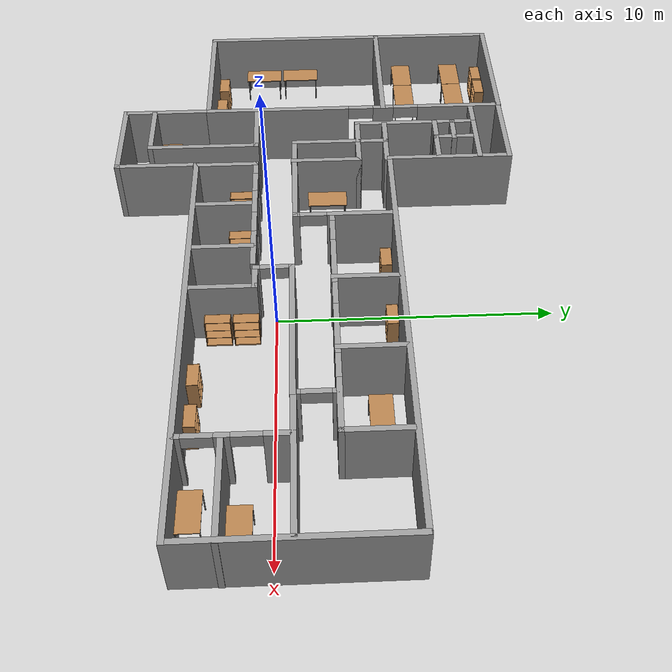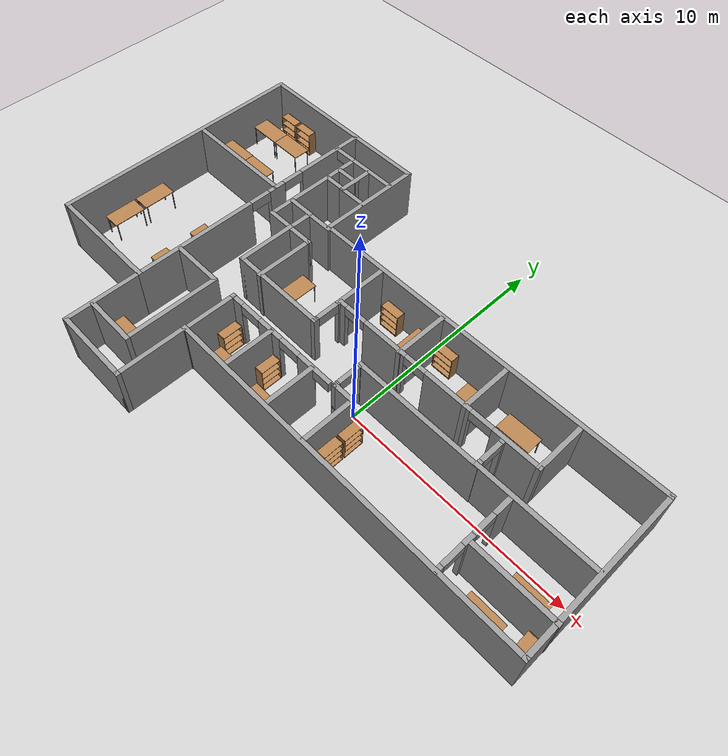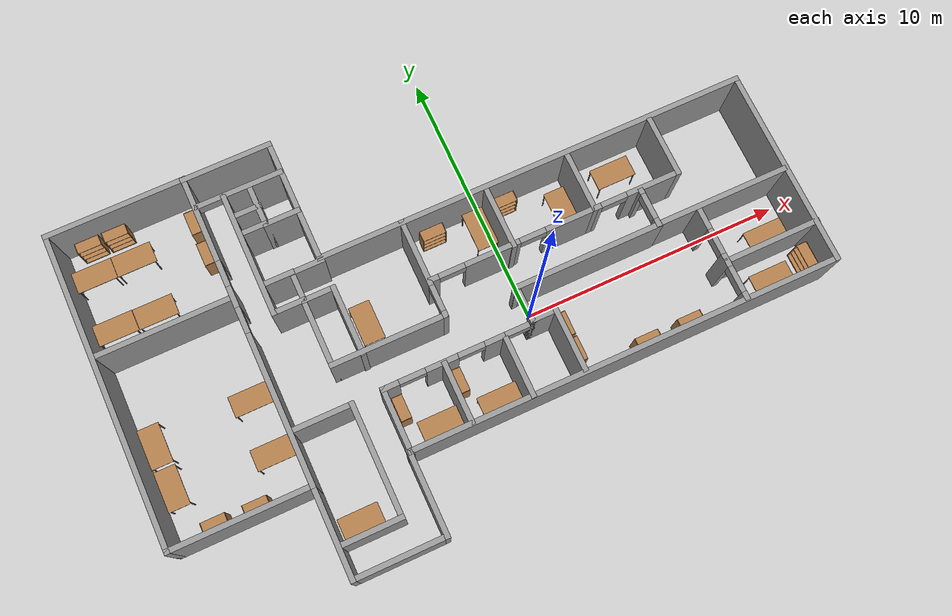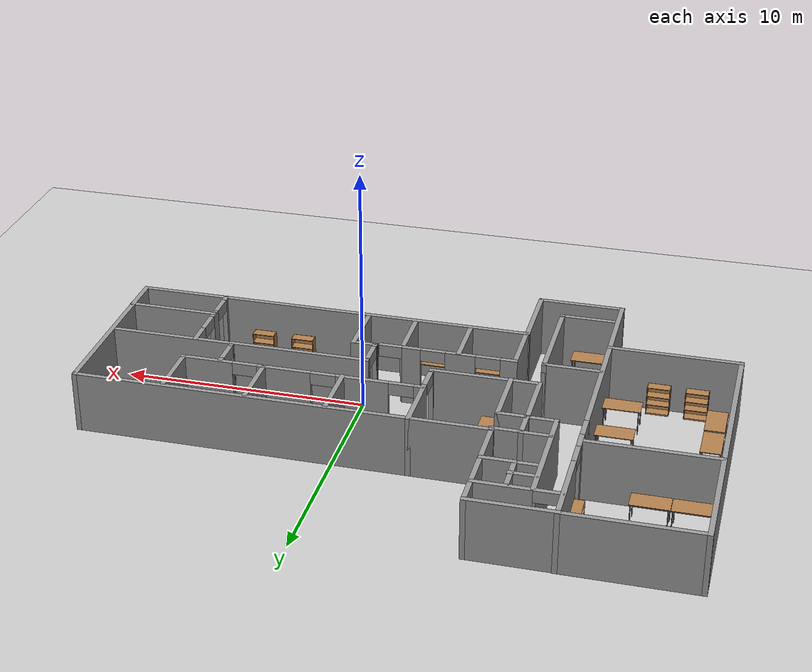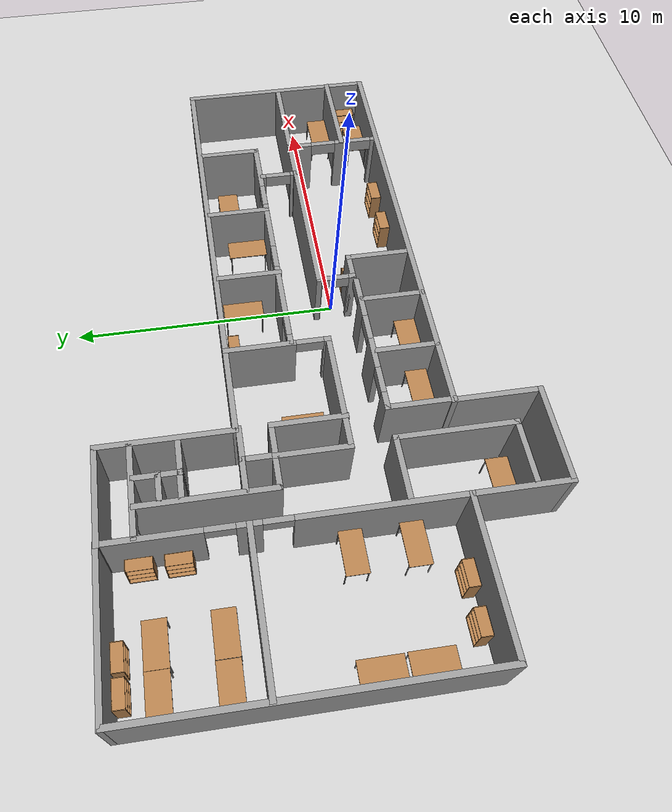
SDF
<sdf version="1.5">
 <world name="default">
  <light name="sun" type="directional">
   <pose>0 0 10 0 -0 0</pose>
   <diffuse>0.8 0.8 0.8 1</diffuse>
   <specular>0.2 0.2 0.2 1</specular>
   <attenuation>
    <range>1000</range>
    <constant>0.9</constant>
    <linear>0.01</linear>
    <quadratic>0.001</quadratic>
   </attenuation>
   <direction>-0.5 0.1 -0.9</direction>
  </light>
  <model name="ground_plane">
   <static>1</static>
   <link name="link">
    <collision name="collision">
     <geometry><plane><normal>0 0 1</normal><size>100 100</size></plane></geometry>
     <surface><friction><ode><mu>100</mu><mu2>50</mu2></ode></friction></surface>
    </collision>
    <visual name="visual">
     <cast_shadows>0</cast_shadows>
     <geometry><plane><normal>0 0 1</normal><size>100 100</size></plane></geometry>
     <material>
      <script><uri>file://media/materials/scripts/gazebo.material</uri><name>Gazebo/Grey</name></script>
     </material>
    </visual>
   </link>
  </model>
  <physics name="default_physics" default="0" type="ode">
   <max_step_size>0.001</max_step_size>
   <real_time_factor>1</real_time_factor>
   <real_time_update_rate>1000</real_time_update_rate>
   <gravity>0 0 -9.8</gravity>
   <magnetic_field>5.5645e-06 2.28758e-05 -4.23884e-05</magnetic_field>
  </physics>
  <scene><ambient>0.4 0.4 0.4 1</ambient><background>0.7 0.7 0.7 1</background><shadows>1</shadows></scene>
  <spherical_coordinates>
   <surface_model>EARTH_WGS84</surface_model>
   <latitude_deg>0</latitude_deg>
   <longitude_deg>0</longitude_deg>
   <elevation>0</elevation>
   <heading_deg>0</heading_deg>
  </spherical_coordinates>
  <model name="CP">
   <link name="Wall_101">
    <collision name="Wall_101_Collision">
     <geometry><box><size>1.30625 0.2 2.5</size></box></geometry>
     <pose>0 0 1.25 0 -0 0</pose>
    </collision>
    <visual name="Wall_101_Visual">
     <pose>0 0 1.25 0 -0 0</pose>
     <geometry><box><size>1.30625 0.2 2.5</size></box></geometry>
     <material>
      <script><uri>file://media/materials/scripts/gazebo.material</uri><name>Gazebo/Grey</name></script>
     </material>
    </visual>
    <pose>-6.6741 3.2611 0 0 -0 0</pose>
   </link>
   <link name="Wall_102">
    <collision name="Wall_102_Collision">
     <geometry><box><size>2.73431 0.2 2.5</size></box></geometry>
     <pose>0 0 1.25 0 -0 0</pose>
    </collision>
    <visual name="Wall_102_Visual">
     <pose>0 0 1.25 0 -0 0</pose>
     <geometry><box><size>2.73431 0.2 2.5</size></box></geometry>
     <material>
      <script><uri>file://media/materials/scripts/gazebo.material</uri><name>Gazebo/Grey</name></script>
     </material>
    </visual>
    <pose>-6.12098 1.99395 0 0 0 -1.5708</pose>
   </link>
   <link name="Wall_104">
    <collision name="Wall_104_Collision">
     <geometry><box><size>1.26602 0.2 2.5</size></box></geometry>
     <pose>0 0 1.25 0 -0 0</pose>
    </collision>
    <visual name="Wall_104_Visual">
     <pose>0 0 1.25 0 -0 0</pose>
     <geometry><box><size>1.26602 0.2 2.5</size></box></geometry>
     <material>
      <script><uri>file://media/materials/scripts/gazebo.material</uri><name>Gazebo/Grey</name></script>
     </material>
    </visual>
    <pose>-7.76023 4.36735 0 0 -0 0</pose>
   </link>
   <link name="Wall_105">
    <collision name="Wall_105_Collision">
     <geometry><box><size>1.24591 0.2 2.5</size></box></geometry>
     <pose>0 0 1.25 0 -0 0</pose>
    </collision>
    <visual name="Wall_105_Visual">
     <pose>0 0 1.25 0 -0 0</pose>
     <geometry><box><size>1.24591 0.2 2.5</size></box></geometry>
     <material>
      <script><uri>file://media/materials/scripts/gazebo.material</uri><name>Gazebo/Grey</name></script>
     </material>
    </visual>
    <pose>-7.22722 3.8444 0 0 0 -1.5708</pose>
   </link>
   <link name="Wall_107">
    <collision name="Wall_107_Collision">
     <geometry><box><size>1.70852 0.2 2.5</size></box></geometry>
     <pose>0 0 1.25 0 -0 0</pose>
    </collision>
    <visual name="Wall_107_Visual">
     <pose>0 0 1.25 0 -0 0</pose>
     <geometry><box><size>1.70852 0.2 2.5</size></box></geometry>
     <material>
      <script><uri>file://media/materials/scripts/gazebo.material</uri><name>Gazebo/Grey</name></script>
     </material>
    </visual>
    <pose>-7.38813 7.13297 0 0 0 -1.5708</pose>
   </link>
   <link name="Wall_108">
    <collision name="Wall_108_Collision">
     <geometry><box><size>1.42693 0.2 2.5</size></box></geometry>
     <pose>0 0 1.25 0 -0 0</pose>
    </collision>
    <visual name="Wall_108_Visual">
     <pose>0 0 1.25 0 -0 0</pose>
     <geometry><box><size>1.42693 0.2 2.5</size></box></geometry>
     <material>
      <script><uri>file://media/materials/scripts/gazebo.material</uri><name>Gazebo/Grey</name></script>
     </material>
    </visual>
    <pose>-6.77467 6.37871 0 0 -0 0</pose>
   </link>
   <link name="Wall_110">
    <collision name="Wall_110_Collision">
     <geometry><box><size>1.14534 0.2 2.5</size></box></geometry>
     <pose>0 0 1.25 0 -0 0</pose>
    </collision>
    <visual name="Wall_110_Visual">
     <pose>0 0 1.25 0 -0 0</pose>
     <geometry><box><size>1.14534 0.2 2.5</size></box></geometry>
     <material>
      <script><uri>file://media/materials/scripts/gazebo.material</uri><name>Gazebo/Grey</name></script>
     </material>
    </visual>
    <pose>-7.82057 7.10279 0 0 -0 0</pose>
   </link>
   <link name="Wall_112">
    <collision name="Wall_112_Collision">
     <geometry><box><size>1.16545 0.2 2.5</size></box></geometry>
     <pose>0 0 1.25 0 -0 0</pose>
    </collision>
    <visual name="Wall_112_Visual">
     <pose>0 0 1.25 0 -0 0</pose>
     <geometry><box><size>1.16545 0.2 2.5</size></box></geometry>
     <material>
      <script><uri>file://media/materials/scripts/gazebo.material</uri><name>Gazebo/Grey</name></script>
     </material>
    </visual>
    <pose>-7.85074 6.39882 0 0 -0 3.14159</pose>
   </link>
   <link name="Wall_114">
    <collision name="Wall_114_Collision">
     <geometry><box><size>1.30625 0.2 2.5</size></box></geometry>
     <pose>0 0 1.25 0 -0 0</pose>
    </collision>
    <visual name="Wall_114_Visual">
     <pose>0 0 1.25 0 -0 0</pose>
     <geometry><box><size>1.30625 0.2 2.5</size></box></geometry>
     <material>
      <script><uri>file://media/materials/scripts/gazebo.material</uri><name>Gazebo/Grey</name></script>
     </material>
    </visual>
    <pose>-6.65399 4.34724 0 0 -0 0</pose>
   </link>
   <link name="Wall_47">
    <collision name="Wall_47_Collision">
     <geometry><box><size>12.0469 0.2 2.5</size></box></geometry>
     <pose>0 0 1.25 0 -0 0</pose>
    </collision>
    <visual name="Wall_47_Visual">
     <pose>0 0 1.25 0 -0 0</pose>
     <geometry><box><size>12.0469 0.2 2.5</size></box></geometry>
     <material>
      <script><uri>file://media/materials/scripts/gazebo.material</uri><name>Gazebo/Grey</name></script>
     </material>
    </visual>
    <pose>-14.5888 3.21082 0 0 0 -1.5708</pose>
   </link>
   <link name="Wall_48">
    <collision name="Wall_48_Collision">
     <geometry><box><size>5.36919 0.2 2.5</size></box></geometry>
     <pose>0 0 1.25 0 -0 0</pose>
    </collision>
    <visual name="Wall_48_Visual">
     <pose>0 0 1.25 0 -0 0</pose>
     <geometry><box><size>5.36919 0.2 2.5</size></box></geometry>
     <material>
      <script><uri>file://media/materials/scripts/gazebo.material</uri><name>Gazebo/Grey</name></script>
     </material>
    </visual>
    <pose>-12.0042 -2.71263 0 0 -0 0</pose>
   </link>
   <link name="Wall_49">
    <pose>-9.4196 3.21082 0 0 -0 1.5708</pose>
    <visual name="Wall_49_Visual_0">
     <pose>-3.12596 0 1.25 0 -0 0</pose>
     <geometry><box><size>5.79498 0.2 2.5</size></box></geometry>
     <material>
      <script><uri>file://media/materials/scripts/gazebo.material</uri><name>Gazebo/Grey</name></script>
     </material>
    </visual>
    <collision name="Wall_49_Collision_0">
     <geometry><box><size>5.79498 0.2 2.5</size></box></geometry>
     <pose>-3.12596 0 1.25 0 -0 0</pose>
    </collision>
    <visual name="Wall_49_Visual_1">
     <pose>1.1867 0 1.25 0 -0 0</pose>
     <geometry><box><size>0.830335 0.2 2.5</size></box></geometry>
     <material>
      <script><uri>file://media/materials/scripts/gazebo.material</uri><name>Gazebo/Grey</name></script>
     </material>
    </visual>
    <collision name="Wall_49_Collision_1">
     <geometry><box><size>0.830335 0.2 2.5</size></box></geometry>
     <pose>1.1867 0 1.25 0 -0 0</pose>
    </collision>
    <visual name="Wall_49_Visual_2">
     <pose>4.31266 0 1.25 0 -0 0</pose>
     <geometry><box><size>3.42158 0.2 2.5</size></box></geometry>
     <material>
      <script><uri>file://media/materials/scripts/gazebo.material</uri><name>Gazebo/Grey</name></script>
     </material>
    </visual>
    <collision name="Wall_49_Collision_2">
     <geometry><box><size>3.42158 0.2 2.5</size></box></geometry>
     <pose>4.31266 0 1.25 0 -0 0</pose>
    </collision>
    <visual name="Wall_49_Visual_3">
     <pose>0.271533 0 2.25 0 -0 0</pose>
     <geometry><box><size>1 0.2 0.5</size></box></geometry>
     <material>
      <script><uri>file://media/materials/scripts/gazebo.material</uri><name>Gazebo/Grey</name></script>
     </material>
    </visual>
    <collision name="Wall_49_Collision_3">
     <geometry><box><size>1 0.2 0.5</size></box></geometry>
     <pose>0.271533 0 2.25 0 -0 0</pose>
    </collision>
    <visual name="Wall_49_Visual_4">
     <pose>2.10187 0 2.25 0 -0 0</pose>
     <geometry><box><size>1 0.2 0.5</size></box></geometry>
     <material>
      <script><uri>file://media/materials/scripts/gazebo.material</uri><name>Gazebo/Grey</name></script>
     </material>
    </visual>
    <collision name="Wall_49_Collision_4">
     <geometry><box><size>1 0.2 0.5</size></box></geometry>
     <pose>2.10187 0 2.25 0 -0 0</pose>
    </collision>
   </link>
   <link name="Wall_50">
    <collision name="Wall_50_Collision">
     <geometry><box><size>5.36919 0.2 2.5</size></box></geometry>
     <pose>0 0 1.25 0 -0 0</pose>
    </collision>
    <visual name="Wall_50_Visual">
     <pose>0 0 1.25 0 -0 0</pose>
     <geometry><box><size>5.36919 0.2 2.5</size></box></geometry>
     <material>
      <script><uri>file://media/materials/scripts/gazebo.material</uri><name>Gazebo/Grey</name></script>
     </material>
    </visual>
    <pose>-12.0042 9.13426 0 0 -0 3.14159</pose>
   </link>
   <link name="Wall_52">
    <collision name="Wall_52_Collision">
     <geometry><box><size>5.32896 0.2 2.5</size></box></geometry>
     <pose>0 0 1.25 0 -0 0</pose>
    </collision>
    <visual name="Wall_52_Visual">
     <pose>0 0 1.25 0 -0 0</pose>
     <geometry><box><size>5.32896 0.2 2.5</size></box></geometry>
     <material>
      <script><uri>file://media/materials/scripts/gazebo.material</uri><name>Gazebo/Grey</name></script>
     </material>
    </visual>
    <pose>-11.9841 4.38746 0 0 -0 0</pose>
   </link>
   <link name="Wall_54">
    <collision name="Wall_54_Collision">
     <geometry><box><size>3.49863 0.2 2.5</size></box></geometry>
     <pose>0 0 1.25 0 -0 0</pose>
    </collision>
    <visual name="Wall_54_Visual">
     <pose>0 0 1.25 0 -0 0</pose>
     <geometry><box><size>3.49863 0.2 2.5</size></box></geometry>
     <material>
      <script><uri>file://media/materials/scripts/gazebo.material</uri><name>Gazebo/Grey</name></script>
     </material>
    </visual>
    <pose>-7.7904 9.11415 0 0 -0 0</pose>
   </link>
   <link name="Wall_55">
    <collision name="Wall_55_Collision">
     <geometry><box><size>4.86635 0.2 2.5</size></box></geometry>
     <pose>0 0 1.25 0 -0 0</pose>
    </collision>
    <visual name="Wall_55_Visual">
     <pose>0 0 1.25 0 -0 0</pose>
     <geometry><box><size>4.86635 0.2 2.5</size></box></geometry>
     <material>
      <script><uri>file://media/materials/scripts/gazebo.material</uri><name>Gazebo/Grey</name></script>
     </material>
    </visual>
    <pose>-6.14109 6.78098 0 0 0 -1.5708</pose>
   </link>
   <link name="Wall_56">
    <collision name="Wall_56_Collision">
     <geometry><box><size>16.6127 0.2 2.5</size></box></geometry>
     <pose>0 0 1.25 0 -0 0</pose>
    </collision>
    <visual name="Wall_56_Visual">
     <pose>0 0 1.25 0 -0 0</pose>
     <geometry><box><size>16.6127 0.2 2.5</size></box></geometry>
     <material>
      <script><uri>file://media/materials/scripts/gazebo.material</uri><name>Gazebo/Grey</name></script>
     </material>
    </visual>
    <pose>2.06525 4.4478 0 0 -0 0</pose>
   </link>
   <link name="Wall_57">
    <collision name="Wall_57_Collision">
     <geometry><box><size>7.66214 0.2 2.5</size></box></geometry>
     <pose>0 0 1.25 0 -0 0</pose>
    </collision>
    <visual name="Wall_57_Visual">
     <pose>0 0 1.25 0 -0 0</pose>
     <geometry><box><size>7.66214 0.2 2.5</size></box></geometry>
     <material>
      <script><uri>file://media/materials/scripts/gazebo.material</uri><name>Gazebo/Grey</name></script>
     </material>
    </visual>
    <pose>10.2716 0.716735 0 0 0 -1.5708</pose>
   </link>
   <link name="Wall_58">
    <collision name="Wall_58_Collision">
     <geometry><box><size>16.5121 0.2 2.5</size></box></geometry>
     <pose>0 0 1.25 0 -0 0</pose>
    </collision>
    <visual name="Wall_58_Visual">
     <pose>0 0 1.25 0 -0 0</pose>
     <geometry><box><size>16.5121 0.2 2.5</size></box></geometry>
     <material>
      <script><uri>file://media/materials/scripts/gazebo.material</uri><name>Gazebo/Grey</name></script>
     </material>
    </visual>
    <pose>2.11553 -3.01433 0 0 -0 3.14159</pose>
   </link>
   <link name="Wall_59">
    <collision name="Wall_59_Collision">
     <geometry><box><size>3.23715 0.2 2.5</size></box></geometry>
     <pose>0 0 1.25 0 -0 0</pose>
    </collision>
    <visual name="Wall_59_Visual">
     <pose>0 0 1.25 0 -0 0</pose>
     <geometry><box><size>3.23715 0.2 2.5</size></box></geometry>
     <material>
      <script><uri>file://media/materials/scripts/gazebo.material</uri><name>Gazebo/Grey</name></script>
     </material>
    </visual>
    <pose>-6.04052 -4.53291 0 0 0 -1.5708</pose>
   </link>
   <link name="Wall_60">
    <collision name="Wall_60_Collision">
     <geometry><box><size>3.57908 0.2 2.5</size></box></geometry>
     <pose>0 0 1.25 0 -0 0</pose>
    </collision>
    <visual name="Wall_60_Visual">
     <pose>0 0 1.25 0 -0 0</pose>
     <geometry><box><size>3.57908 0.2 2.5</size></box></geometry>
     <material>
      <script><uri>file://media/materials/scripts/gazebo.material</uri><name>Gazebo/Grey</name></script>
     </material>
    </visual>
    <pose>-7.73006 -6.05148 0 0 -0 3.14159</pose>
   </link>
   <link name="Wall_61">
    <collision name="Wall_61_Collision">
     <geometry><box><size>3.35783 0.2 2.5</size></box></geometry>
     <pose>0 0 1.25 0 -0 0</pose>
    </collision>
    <visual name="Wall_61_Visual">
     <pose>0 0 1.25 0 -0 0</pose>
     <geometry><box><size>3.35783 0.2 2.5</size></box></geometry>
     <material>
      <script><uri>file://media/materials/scripts/gazebo.material</uri><name>Gazebo/Grey</name></script>
     </material>
    </visual>
    <pose>-9.4196 -4.47257 0 0 -0 1.5708</pose>
   </link>
   <link name="Wall_63">
    <pose>-7.77029 7.96768 0 0 -0 0</pose>
    <visual name="Wall_63_Visual_0">
     <pose>-1.63755 0 1.25 0 -0 0</pose>
     <geometry><box><size>0.102839 0.2 2.5</size></box></geometry>
     <material>
      <script><uri>file://media/materials/scripts/gazebo.material</uri><name>Gazebo/Grey</name></script>
     </material>
    </visual>
    <collision name="Wall_63_Collision_0">
     <geometry><box><size>0.102839 0.2 2.5</size></box></geometry>
     <pose>-1.63755 0 1.25 0 -0 0</pose>
    </collision>
    <visual name="Wall_63_Visual_1">
     <pose>0.55142 0 1.25 0 -0 0</pose>
     <geometry><box><size>2.2751 0.2 2.5</size></box></geometry>
     <material>
      <script><uri>file://media/materials/scripts/gazebo.material</uri><name>Gazebo/Grey</name></script>
     </material>
    </visual>
    <collision name="Wall_63_Collision_1">
     <geometry><box><size>2.2751 0.2 2.5</size></box></geometry>
     <pose>0.55142 0 1.25 0 -0 0</pose>
    </collision>
    <visual name="Wall_63_Visual_2">
     <pose>-1.08613 0 2.25 0 -0 0</pose>
     <geometry><box><size>1 0.2 0.5</size></box></geometry>
     <material>
      <script><uri>file://media/materials/scripts/gazebo.material</uri><name>Gazebo/Grey</name></script>
     </material>
    </visual>
    <collision name="Wall_63_Collision_2">
     <geometry><box><size>1 0.2 0.5</size></box></geometry>
     <pose>-1.08613 0 2.25 0 -0 0</pose>
    </collision>
   </link>
   <link name="Wall_65">
    <collision name="Wall_65_Collision">
     <geometry><box><size>4.82612 0.2 2.5</size></box></geometry>
     <pose>0 0 1.25 0 -0 0</pose>
    </collision>
    <visual name="Wall_65_Visual">
     <pose>0 0 1.25 0 -0 0</pose>
     <geometry><box><size>4.82612 0.2 2.5</size></box></geometry>
     <material>
      <script><uri>file://media/materials/scripts/gazebo.material</uri><name>Gazebo/Grey</name></script>
     </material>
    </visual>
    <pose>-8.35358 5.59428 0 0 0 -1.5708</pose>
   </link>
   <link name="Wall_66">
    <collision name="Wall_66_Collision">
     <geometry><box><size>1.30625 0.2 2.5</size></box></geometry>
     <pose>0 0 1.25 0 -0 0</pose>
    </collision>
    <visual name="Wall_66_Visual">
     <pose>0 0 1.25 0 -0 0</pose>
     <geometry><box><size>1.30625 0.2 2.5</size></box></geometry>
     <material>
      <script><uri>file://media/materials/scripts/gazebo.material</uri><name>Gazebo/Grey</name></script>
     </material>
    </visual>
    <pose>-7.80046 3.28121 0 0 -0 0</pose>
   </link>
   <link name="Wall_67">
    <collision name="Wall_67_Collision">
     <geometry><box><size>2.7142 0.2 2.5</size></box></geometry>
     <pose>0 0 1.25 0 -0 0</pose>
    </collision>
    <visual name="Wall_67_Visual">
     <pose>0 0 1.25 0 -0 0</pose>
     <geometry><box><size>2.7142 0.2 2.5</size></box></geometry>
     <material>
      <script><uri>file://media/materials/scripts/gazebo.material</uri><name>Gazebo/Grey</name></script>
     </material>
    </visual>
    <pose>-7.24734 2.02412 0 0 0 -1.5708</pose>
   </link>
   <link name="Wall_68">
    <collision name="Wall_68_Collision">
     <geometry><box><size>4.44396 0.2 2.5</size></box></geometry>
     <pose>0 0 1.25 0 -0 0</pose>
    </collision>
    <visual name="Wall_68_Visual">
     <pose>0 0 1.25 0 -0 0</pose>
     <geometry><box><size>4.44396 0.2 2.5</size></box></geometry>
     <material>
      <script><uri>file://media/materials/scripts/gazebo.material</uri><name>Gazebo/Grey</name></script>
     </material>
    </visual>
    <pose>-5.12535 0.767019 0 0 -0 0</pose>
   </link>
   <link name="Wall_69">
    <pose>-3.00337 2.60741 0 0 -0 1.5708</pose>
    <visual name="Wall_69_Visual_0">
     <pose>-1.80852 0 1.25 0 -0 0</pose>
     <geometry><box><size>0.263748 0.2 2.5</size></box></geometry>
     <material>
      <script><uri>file://media/materials/scripts/gazebo.material</uri><name>Gazebo/Grey</name></script>
     </material>
    </visual>
    <collision name="Wall_69_Collision_0">
     <geometry><box><size>0.263748 0.2 2.5</size></box></geometry>
     <pose>-1.80852 0 1.25 0 -0 0</pose>
    </collision>
    <visual name="Wall_69_Visual_1">
     <pose>0.631874 0 1.25 0 -0 0</pose>
     <geometry><box><size>2.61704 0.2 2.5</size></box></geometry>
     <material>
      <script><uri>file://media/materials/scripts/gazebo.material</uri><name>Gazebo/Grey</name></script>
     </material>
    </visual>
    <collision name="Wall_69_Collision_1">
     <geometry><box><size>2.61704 0.2 2.5</size></box></geometry>
     <pose>0.631874 0 1.25 0 -0 0</pose>
    </collision>
    <visual name="Wall_69_Visual_2">
     <pose>-1.17664 0 2.25 0 -0 0</pose>
     <geometry><box><size>1 0.2 0.5</size></box></geometry>
     <material>
      <script><uri>file://media/materials/scripts/gazebo.material</uri><name>Gazebo/Grey</name></script>
     </material>
    </visual>
    <collision name="Wall_69_Collision_2">
     <geometry><box><size>1 0.2 0.5</size></box></geometry>
     <pose>-1.17664 0 2.25 0 -0 0</pose>
    </collision>
   </link>
   <link name="Wall_71">
    <pose>1.87417 2.11463 0 0 -0 0</pose>
    <visual name="Wall_71_Visual_0">
     <pose>-4.71493 0 1.25 0 -0 0</pose>
     <geometry><box><size>0.404543 0.2 2.5</size></box></geometry>
     <material>
      <script><uri>file://media/materials/scripts/gazebo.material</uri><name>Gazebo/Grey</name></script>
     </material>
    </visual>
    <collision name="Wall_71_Collision_0">
     <geometry><box><size>0.404543 0.2 2.5</size></box></geometry>
     <pose>-4.71493 0 1.25 0 -0 0</pose>
    </collision>
    <visual name="Wall_71_Visual_1">
     <pose>-2.45386 0 1.25 0 -0 0</pose>
     <geometry><box><size>2.1176 0.2 2.5</size></box></geometry>
     <material>
      <script><uri>file://media/materials/scripts/gazebo.material</uri><name>Gazebo/Grey</name></script>
     </material>
    </visual>
    <collision name="Wall_71_Collision_1">
     <geometry><box><size>2.1176 0.2 2.5</size></box></geometry>
     <pose>-2.45386 0 1.25 0 -0 0</pose>
    </collision>
    <visual name="Wall_71_Visual_2">
     <pose>0.693918 0 1.25 0 -0 0</pose>
     <geometry><box><size>2.17794 0.2 2.5</size></box></geometry>
     <material>
      <script><uri>file://media/materials/scripts/gazebo.material</uri><name>Gazebo/Grey</name></script>
     </material>
    </visual>
    <collision name="Wall_71_Collision_2">
     <geometry><box><size>2.17794 0.2 2.5</size></box></geometry>
     <pose>0.693918 0 1.25 0 -0 0</pose>
    </collision>
    <visual name="Wall_71_Visual_3">
     <pose>3.85005 0 1.25 0 -0 0</pose>
     <geometry><box><size>2.13431 0.2 2.5</size></box></geometry>
     <material>
      <script><uri>file://media/materials/scripts/gazebo.material</uri><name>Gazebo/Grey</name></script>
     </material>
    </visual>
    <collision name="Wall_71_Collision_3">
     <geometry><box><size>2.13431 0.2 2.5</size></box></geometry>
     <pose>3.85005 0 1.25 0 -0 0</pose>
    </collision>
    <visual name="Wall_71_Visual_4">
     <pose>-4.01266 0 2.25 0 -0 0</pose>
     <geometry><box><size>1 0.2 0.5</size></box></geometry>
     <material>
      <script><uri>file://media/materials/scripts/gazebo.material</uri><name>Gazebo/Grey</name></script>
     </material>
    </visual>
    <collision name="Wall_71_Collision_4">
     <geometry><box><size>1 0.2 0.5</size></box></geometry>
     <pose>-4.01266 0 2.25 0 -0 0</pose>
    </collision>
    <visual name="Wall_71_Visual_5">
     <pose>-0.895054 0 2.25 0 -0 0</pose>
     <geometry><box><size>1 0.2 0.5</size></box></geometry>
     <material>
      <script><uri>file://media/materials/scripts/gazebo.material</uri><name>Gazebo/Grey</name></script>
     </material>
    </visual>
    <collision name="Wall_71_Collision_5">
     <geometry><box><size>1 0.2 0.5</size></box></geometry>
     <pose>-0.895054 0 2.25 0 -0 0</pose>
    </collision>
    <visual name="Wall_71_Visual_6">
     <pose>2.28289 0 2.25 0 -0 0</pose>
     <geometry><box><size>1 0.2 0.5</size></box></geometry>
     <material>
      <script><uri>file://media/materials/scripts/gazebo.material</uri><name>Gazebo/Grey</name></script>
     </material>
    </visual>
    <collision name="Wall_71_Collision_6">
     <geometry><box><size>1 0.2 0.5</size></box></geometry>
     <pose>2.28289 0 2.25 0 -0 0</pose>
    </collision>
   </link>
   <link name="Wall_72">
    <collision name="Wall_72_Collision">
     <geometry><box><size>2.37227 0.2 2.5</size></box></geometry>
     <pose>0 0 1.25 0 -0 0</pose>
    </collision>
    <visual name="Wall_72_Visual">
     <pose>0 0 1.25 0 -0 0</pose>
     <geometry><box><size>2.37227 0.2 2.5</size></box></geometry>
     <material>
      <script><uri>file://media/materials/scripts/gazebo.material</uri><name>Gazebo/Grey</name></script>
     </material>
    </visual>
    <pose>6.69137 3.20076 0 0 -0 1.5708</pose>
   </link>
   <link name="Wall_74">
    <collision name="Wall_74_Collision">
     <geometry><box><size>2.45272 0.2 2.5</size></box></geometry>
     <pose>0 0 1.25 0 -0 0</pose>
    </collision>
    <visual name="Wall_74_Visual">
     <pose>0 0 1.25 0 -0 0</pose>
     <geometry><box><size>2.45272 0.2 2.5</size></box></geometry>
     <material>
      <script><uri>file://media/materials/scripts/gazebo.material</uri><name>Gazebo/Grey</name></script>
     </material>
    </visual>
    <pose>0.214799 3.20076 0 0 -0 1.5708</pose>
   </link>
   <link name="Wall_76">
    <collision name="Wall_76_Collision">
     <geometry><box><size>2.43261 0.2 2.5</size></box></geometry>
     <pose>0 0 1.25 0 -0 0</pose>
    </collision>
    <visual name="Wall_76_Visual">
     <pose>0 0 1.25 0 -0 0</pose>
     <geometry><box><size>2.43261 0.2 2.5</size></box></geometry>
     <material>
      <script><uri>file://media/materials/scripts/gazebo.material</uri><name>Gazebo/Grey</name></script>
     </material>
    </visual>
    <pose>3.39274 3.23093 0 0 -0 1.5708</pose>
   </link>
   <link name="Wall_78">
    <pose>5.18285 1.34026 0 0 0 -1.5708</pose>
    <visual name="Wall_78_Visual_0">
     <pose>-0.662044 0 1.25 0 -0 0</pose>
     <geometry><box><size>0.223521 0.2 2.5</size></box></geometry>
     <material>
      <script><uri>file://media/materials/scripts/gazebo.material</uri><name>Gazebo/Grey</name></script>
     </material>
    </visual>
    <collision name="Wall_78_Collision_0">
     <geometry><box><size>0.223521 0.2 2.5</size></box></geometry>
     <pose>-0.662044 0 1.25 0 -0 0</pose>
    </collision>
    <visual name="Wall_78_Visual_1">
     <pose>0.61176 0 1.25 0 -0 0</pose>
     <geometry><box><size>0.324089 0.2 2.5</size></box></geometry>
     <material>
      <script><uri>file://media/materials/scripts/gazebo.material</uri><name>Gazebo/Grey</name></script>
     </material>
    </visual>
    <collision name="Wall_78_Collision_1">
     <geometry><box><size>0.324089 0.2 2.5</size></box></geometry>
     <pose>0.61176 0 1.25 0 -0 0</pose>
    </collision>
    <visual name="Wall_78_Visual_2">
     <pose>-0.050284 0 2.25 0 -0 0</pose>
     <geometry><box><size>1 0.2 0.5</size></box></geometry>
     <material>
      <script><uri>file://media/materials/scripts/gazebo.material</uri><name>Gazebo/Grey</name></script>
     </material>
    </visual>
    <collision name="Wall_78_Collision_2">
     <geometry><box><size>1 0.2 0.5</size></box></geometry>
     <pose>-0.050284 0 2.25 0 -0 0</pose>
    </collision>
   </link>
   <link name="Wall_79">
    <collision name="Wall_79_Collision">
     <geometry><box><size>5.18817 0.2 2.5</size></box></geometry>
     <pose>0 0 1.25 0 -0 0</pose>
    </collision>
    <visual name="Wall_79_Visual">
     <pose>0 0 1.25 0 -0 0</pose>
     <geometry><box><size>5.18817 0.2 2.5</size></box></geometry>
     <material>
      <script><uri>file://media/materials/scripts/gazebo.material</uri><name>Gazebo/Grey</name></script>
     </material>
    </visual>
    <pose>7.67693 0.666451 0 0 -0 0</pose>
   </link>
   <link name="Wall_81">
    <collision name="Wall_81_Collision">
     <geometry><box><size>5.75135 0.2 2.5</size></box></geometry>
     <pose>0 0 1.25 0 -0 0</pose>
    </collision>
    <visual name="Wall_81_Visual">
     <pose>0 0 1.25 0 -0 0</pose>
     <geometry><box><size>5.75135 0.2 2.5</size></box></geometry>
     <material>
      <script><uri>file://media/materials/scripts/gazebo.material</uri><name>Gazebo/Grey</name></script>
     </material>
    </visual>
    <pose>2.42729 0.646338 0 0 -0 3.14159</pose>
   </link>
   <link name="Wall_82">
    <pose>-0.348381 0.002703 0 0 0 -1.5708</pose>
    <visual name="Wall_82_Visual_0">
     <pose>-0.631874 0 1.25 0 -0 0</pose>
     <geometry><box><size>0.223521 0.2 2.5</size></box></geometry>
     <material>
      <script><uri>file://media/materials/scripts/gazebo.material</uri><name>Gazebo/Grey</name></script>
     </material>
    </visual>
    <collision name="Wall_82_Collision_0">
     <geometry><box><size>0.223521 0.2 2.5</size></box></geometry>
     <pose>-0.631874 0 1.25 0 -0 0</pose>
    </collision>
    <visual name="Wall_82_Visual_1">
     <pose>0.61176 0 1.25 0 -0 0</pose>
     <geometry><box><size>0.263748 0.2 2.5</size></box></geometry>
     <material>
      <script><uri>file://media/materials/scripts/gazebo.material</uri><name>Gazebo/Grey</name></script>
     </material>
    </visual>
    <collision name="Wall_82_Collision_1">
     <geometry><box><size>0.263748 0.2 2.5</size></box></geometry>
     <pose>0.61176 0 1.25 0 -0 0</pose>
    </collision>
    <visual name="Wall_82_Visual_2">
     <pose>-0.020114 0 2.25 0 -0 0</pose>
     <geometry><box><size>1 0.2 0.5</size></box></geometry>
     <material>
      <script><uri>file://media/materials/scripts/gazebo.material</uri><name>Gazebo/Grey</name></script>
     </material>
    </visual>
    <collision name="Wall_82_Collision_2">
     <geometry><box><size>1 0.2 0.5</size></box></geometry>
     <pose>-0.020114 0 2.25 0 -0 0</pose>
    </collision>
   </link>
   <link name="Wall_83">
    <collision name="Wall_83_Collision">
     <geometry><box><size>1.085 0.2 2.5</size></box></geometry>
     <pose>0 0 1.25 0 -0 0</pose>
    </collision>
    <visual name="Wall_83_Visual">
     <pose>0 0 1.25 0 -0 0</pose>
     <geometry><box><size>1.085 0.2 2.5</size></box></geometry>
     <material>
      <script><uri>file://media/materials/scripts/gazebo.material</uri><name>Gazebo/Grey</name></script>
     </material>
    </visual>
    <pose>0.094117 -0.640931 0 0 -0 0</pose>
   </link>
   <link name="Wall_84">
    <collision name="Wall_84_Collision">
     <geometry><box><size>2.47283 0.2 2.5</size></box></geometry>
     <pose>0 0 1.25 0 -0 0</pose>
    </collision>
    <visual name="Wall_84_Visual">
     <pose>0 0 1.25 0 -0 0</pose>
     <geometry><box><size>2.47283 0.2 2.5</size></box></geometry>
     <material>
      <script><uri>file://media/materials/scripts/gazebo.material</uri><name>Gazebo/Grey</name></script>
     </material>
    </visual>
    <pose>0.536616 -1.77735 0 0 0 -1.5708</pose>
   </link>
   <link name="Wall_86">
    <collision name="Wall_86_Collision">
     <geometry><box><size>2.51306 0.2 2.5</size></box></geometry>
     <pose>0 0 1.25 0 -0 0</pose>
    </collision>
    <visual name="Wall_86_Visual">
     <pose>0 0 1.25 0 -0 0</pose>
     <geometry><box><size>2.51306 0.2 2.5</size></box></geometry>
     <material>
      <script><uri>file://media/materials/scripts/gazebo.material</uri><name>Gazebo/Grey</name></script>
     </material>
    </visual>
    <pose>-6.0003 -1.87792 0 0 -0 1.5708</pose>
   </link>
   <link name="Wall_87">
    <pose>-3.30508 -0.721385 0 0 -0 0</pose>
    <visual name="Wall_87_Visual_0">
     <pose>-2.45215 0 1.25 0 -0 0</pose>
     <geometry><box><size>0.686133 0.2 2.5</size></box></geometry>
     <material>
      <script><uri>file://media/materials/scripts/gazebo.material</uri><name>Gazebo/Grey</name></script>
     </material>
    </visual>
    <collision name="Wall_87_Collision_0">
     <geometry><box><size>0.686133 0.2 2.5</size></box></geometry>
     <pose>-2.45215 0 1.25 0 -0 0</pose>
    </collision>
    <visual name="Wall_87_Visual_1">
     <pose>-0.502839 0 1.25 0 -0 0</pose>
     <geometry><box><size>1.21249 0.2 2.5</size></box></geometry>
     <material>
      <script><uri>file://media/materials/scripts/gazebo.material</uri><name>Gazebo/Grey</name></script>
     </material>
    </visual>
    <collision name="Wall_87_Collision_1">
     <geometry><box><size>1.21249 0.2 2.5</size></box></geometry>
     <pose>-0.502839 0 1.25 0 -0 0</pose>
    </collision>
    <visual name="Wall_87_Visual_2">
     <pose>1.4884 0 1.25 0 -0 0</pose>
     <geometry><box><size>0.769994 0.2 2.5</size></box></geometry>
     <material>
      <script><uri>file://media/materials/scripts/gazebo.material</uri><name>Gazebo/Grey</name></script>
     </material>
    </visual>
    <collision name="Wall_87_Collision_2">
     <geometry><box><size>0.769994 0.2 2.5</size></box></geometry>
     <pose>1.4884 0 1.25 0 -0 0</pose>
    </collision>
    <visual name="Wall_87_Visual_3">
     <pose>-1.60909 0 2.25 0 -0 0</pose>
     <geometry><box><size>1 0.2 0.5</size></box></geometry>
     <material>
      <script><uri>file://media/materials/scripts/gazebo.material</uri><name>Gazebo/Grey</name></script>
     </material>
    </visual>
    <collision name="Wall_87_Collision_3">
     <geometry><box><size>1 0.2 0.5</size></box></geometry>
     <pose>-1.60909 0 2.25 0 -0 0</pose>
    </collision>
    <visual name="Wall_87_Visual_4">
     <pose>0.603407 0 2.25 0 -0 0</pose>
     <geometry><box><size>1 0.2 0.5</size></box></geometry>
     <material>
      <script><uri>file://media/materials/scripts/gazebo.material</uri><name>Gazebo/Grey</name></script>
     </material>
    </visual>
    <collision name="Wall_87_Collision_4">
     <geometry><box><size>1 0.2 0.5</size></box></geometry>
     <pose>0.603407 0 2.25 0 -0 0</pose>
    </collision>
    <visual name="Wall_87_Visual_5">
     <pose>2.33431 0 2.25 0 -0 0</pose>
     <geometry><box><size>0.921817 0.2 0.5</size></box></geometry>
     <material>
      <script><uri>file://media/materials/scripts/gazebo.material</uri><name>Gazebo/Grey</name></script>
     </material>
    </visual>
    <collision name="Wall_87_Collision_5">
     <geometry><box><size>0.921817 0.2 0.5</size></box></geometry>
     <pose>2.33431 0 2.25 0 -0 0</pose>
    </collision>
   </link>
   <link name="Wall_89">
    <collision name="Wall_89_Collision">
     <geometry><box><size>2.39238 0.2 2.5</size></box></geometry>
     <pose>0 0 1.25 0 -0 0</pose>
    </collision>
    <visual name="Wall_89_Visual">
     <pose>0 0 1.25 0 -0 0</pose>
     <geometry><box><size>2.39238 0.2 2.5</size></box></geometry>
     <material>
      <script><uri>file://media/materials/scripts/gazebo.material</uri><name>Gazebo/Grey</name></script>
     </material>
    </visual>
    <pose>-1.45463 -1.89803 0 0 0 -1.5708</pose>
   </link>
   <link name="Wall_91">
    <collision name="Wall_91_Collision">
     <geometry><box><size>2.39238 0.2 2.5</size></box></geometry>
     <pose>0 0 1.25 0 -0 0</pose>
    </collision>
    <visual name="Wall_91_Visual">
     <pose>0 0 1.25 0 -0 0</pose>
     <geometry><box><size>2.39238 0.2 2.5</size></box></geometry>
     <material>
      <script><uri>file://media/materials/scripts/gazebo.material</uri><name>Gazebo/Grey</name></script>
     </material>
    </visual>
    <pose>-3.72746 -1.87792 0 0 0 -1.5708</pose>
   </link>
   <link name="Wall_93">
    <collision name="Wall_93_Collision">
     <geometry><box><size>2.39238 0.2 2.5</size></box></geometry>
     <pose>0 0 1.25 0 -0 0</pose>
    </collision>
    <visual name="Wall_93_Visual">
     <pose>0 0 1.25 0 -0 0</pose>
     <geometry><box><size>2.39238 0.2 2.5</size></box></geometry>
     <material>
      <script><uri>file://media/materials/scripts/gazebo.material</uri><name>Gazebo/Grey</name></script>
     </material>
    </visual>
    <pose>-8.24296 -0.741499 0 0 -0 0</pose>
   </link>
   <link name="Wall_94">
    <collision name="Wall_94_Collision">
     <geometry><box><size>4.3434 0.2 2.5</size></box></geometry>
     <pose>0 0 1.25 0 -0 0</pose>
    </collision>
    <visual name="Wall_94_Visual">
     <pose>0 0 1.25 0 -0 0</pose>
     <geometry><box><size>4.3434 0.2 2.5</size></box></geometry>
     <material>
      <script><uri>file://media/materials/scripts/gazebo.material</uri><name>Gazebo/Grey</name></script>
     </material>
    </visual>
    <pose>-7.14677 -2.8132 0 0 0 -1.5708</pose>
   </link>
   <link name="Wall_95">
    <collision name="Wall_95_Collision">
     <geometry><box><size>2.39238 0.2 2.5</size></box></geometry>
     <pose>0 0 1.25 0 -0 0</pose>
    </collision>
    <visual name="Wall_95_Visual">
     <pose>0 0 1.25 0 -0 0</pose>
     <geometry><box><size>2.39238 0.2 2.5</size></box></geometry>
     <material>
      <script><uri>file://media/materials/scripts/gazebo.material</uri><name>Gazebo/Grey</name></script>
     </material>
    </visual>
    <pose>-8.24296 -4.8849 0 0 -0 3.14159</pose>
   </link>
   <link name="Wall_97">
    <pose>6.7316 -1.15383 0 0 0 -1.5708</pose>
    <visual name="Wall_97_Visual_0">
     <pose>-1.4163 0 1.25 0 -0 0</pose>
     <geometry><box><size>1.00795 0.2 2.5</size></box></geometry>
     <material>
      <script><uri>file://media/materials/scripts/gazebo.material</uri><name>Gazebo/Grey</name></script>
     </material>
    </visual>
    <collision name="Wall_97_Collision_0">
     <geometry><box><size>1.00795 0.2 2.5</size></box></geometry>
     <pose>-1.4163 0 1.25 0 -0 0</pose>
    </collision>
    <visual name="Wall_97_Visual_1">
     <pose>0.341931 0 1.25 0 -0 0</pose>
     <geometry><box><size>0.508518 0.2 2.5</size></box></geometry>
     <material>
      <script><uri>file://media/materials/scripts/gazebo.material</uri><name>Gazebo/Grey</name></script>
     </material>
    </visual>
    <collision name="Wall_97_Collision_1">
     <geometry><box><size>0.508518 0.2 2.5</size></box></geometry>
     <pose>0.341931 0 1.25 0 -0 0</pose>
    </collision>
    <visual name="Wall_97_Visual_2">
     <pose>1.75823 0 1.25 0 -0 0</pose>
     <geometry><box><size>0.324089 0.2 2.5</size></box></geometry>
     <material>
      <script><uri>file://media/materials/scripts/gazebo.material</uri><name>Gazebo/Grey</name></script>
     </material>
    </visual>
    <collision name="Wall_97_Collision_2">
     <geometry><box><size>0.324089 0.2 2.5</size></box></geometry>
     <pose>1.75823 0 1.25 0 -0 0</pose>
    </collision>
    <visual name="Wall_97_Visual_3">
     <pose>-0.412328 0 2.25 0 -0 0</pose>
     <geometry><box><size>1 0.2 0.5</size></box></geometry>
     <material>
      <script><uri>file://media/materials/scripts/gazebo.material</uri><name>Gazebo/Grey</name></script>
     </material>
    </visual>
    <collision name="Wall_97_Collision_3">
     <geometry><box><size>1 0.2 0.5</size></box></geometry>
     <pose>-0.412328 0 2.25 0 -0 0</pose>
    </collision>
    <visual name="Wall_97_Visual_4">
     <pose>1.09619 0 2.25 0 -0 0</pose>
     <geometry><box><size>1 0.2 0.5</size></box></geometry>
     <material>
      <script><uri>file://media/materials/scripts/gazebo.material</uri><name>Gazebo/Grey</name></script>
     </material>
    </visual>
    <collision name="Wall_97_Collision_4">
     <geometry><box><size>1 0.2 0.5</size></box></geometry>
     <pose>1.09619 0 2.25 0 -0 0</pose>
    </collision>
   </link>
   <link name="Wall_99">
    <collision name="Wall_99_Collision">
     <geometry><box><size>3.71988 0.2 2.5</size></box></geometry>
     <pose>0 0 1.25 0 -0 0</pose>
    </collision>
    <visual name="Wall_99_Visual">
     <pose>0 0 1.25 0 -0 0</pose>
     <geometry><box><size>3.71988 0.2 2.5</size></box></geometry>
     <material>
      <script><uri>file://media/materials/scripts/gazebo.material</uri><name>Gazebo/Grey</name></script>
     </material>
    </visual>
    <pose>8.53176 -1.52593 0 0 -0 0</pose>
   </link>
   <static>1</static>
  </model>
  <model name="table_3">
   <static>1</static>
   <link name="link">
    <collision name="surface">
     <pose>0 0 1 0 -0 0</pose>
     <geometry><box><size>1.5 0.8 0.03</size></box></geometry>
     <surface><friction><ode><mu>0.6</mu><mu2>0.6</mu2></ode></friction></surface>
    </collision>
    <visual name="visual1">
     <pose>0 0 1 0 -0 0</pose>
     <geometry><box><size>1.5 0.8 0.03</size></box></geometry>
     <material>
      <script><uri>file://media/materials/scripts/gazebo.material</uri><name>Gazebo/Wood</name></script>
     </material>
    </visual>
    <collision name="front_left_leg">
     <pose>0.68 0.38 0.5 0 -0 0</pose>
     <geometry><cylinder><radius>0.02</radius><length>1</length></cylinder></geometry>
    </collision>
    <visual name="front_left_leg">
     <pose>0.68 0.38 0.5 0 -0 0</pose>
     <geometry><cylinder><radius>0.02</radius><length>1</length></cylinder></geometry>
     <material>
      <script><uri>file://media/materials/scripts/gazebo.material</uri><name>Gazebo/Grey</name></script>
     </material>
    </visual>
    <collision name="front_right_leg">
     <pose>0.68 -0.38 0.5 0 -0 0</pose>
     <geometry><cylinder><radius>0.02</radius><length>1</length></cylinder></geometry>
    </collision>
    <visual name="front_right_leg">
     <pose>0.68 -0.38 0.5 0 -0 0</pose>
     <geometry><cylinder><radius>0.02</radius><length>1</length></cylinder></geometry>
     <material>
      <script><uri>file://media/materials/scripts/gazebo.material</uri><name>Gazebo/Grey</name></script>
     </material>
    </visual>
    <collision name="back_right_leg">
     <pose>-0.68 -0.38 0.5 0 -0 0</pose>
     <geometry><cylinder><radius>0.02</radius><length>1</length></cylinder></geometry>
    </collision>
    <visual name="back_right_leg">
     <pose>-0.68 -0.38 0.5 0 -0 0</pose>
     <geometry><cylinder><radius>0.02</radius><length>1</length></cylinder></geometry>
     <material>
      <script><uri>file://media/materials/scripts/gazebo.material</uri><name>Gazebo/Grey</name></script>
     </material>
    </visual>
    <collision name="back_left_leg">
     <pose>-0.68 0.38 0.5 0 -0 0</pose>
     <geometry><cylinder><radius>0.02</radius><length>1</length></cylinder></geometry>
    </collision>
    <visual name="back_left_leg">
     <pose>-0.68 0.38 0.5 0 -0 0</pose>
     <geometry><cylinder><radius>0.02</radius><length>1</length></cylinder></geometry>
     <material>
      <script><uri>file://media/materials/scripts/gazebo.material</uri><name>Gazebo/Grey</name></script>
     </material>
    </visual>
   </link>
   <pose>-13.7373 7.65628 0 0 -0 0</pose>
  </model>
  <model name="table_4">
   <static>1</static>
   <link name="link">
    <collision name="surface">
     <pose>0 0 1 0 -0 0</pose>
     <geometry><box><size>1.5 0.8 0.03</size></box></geometry>
     <surface><friction><ode><mu>0.6</mu><mu2>0.6</mu2></ode></friction></surface>
    </collision>
    <visual name="visual1">
     <pose>0 0 1 0 -0 0</pose>
     <geometry><box><size>1.5 0.8 0.03</size></box></geometry>
     <material>
      <script><uri>file://media/materials/scripts/gazebo.material</uri><name>Gazebo/Wood</name></script>
     </material>
    </visual>
    <collision name="front_left_leg">
     <pose>0.68 0.38 0.5 0 -0 0</pose>
     <geometry><cylinder><radius>0.02</radius><length>1</length></cylinder></geometry>
    </collision>
    <visual name="front_left_leg">
     <pose>0.68 0.38 0.5 0 -0 0</pose>
     <geometry><cylinder><radius>0.02</radius><length>1</length></cylinder></geometry>
     <material>
      <script><uri>file://media/materials/scripts/gazebo.material</uri><name>Gazebo/Grey</name></script>
     </material>
    </visual>
    <collision name="front_right_leg">
     <pose>0.68 -0.38 0.5 0 -0 0</pose>
     <geometry><cylinder><radius>0.02</radius><length>1</length></cylinder></geometry>
    </collision>
    <visual name="front_right_leg">
     <pose>0.68 -0.38 0.5 0 -0 0</pose>
     <geometry><cylinder><radius>0.02</radius><length>1</length></cylinder></geometry>
     <material>
      <script><uri>file://media/materials/scripts/gazebo.material</uri><name>Gazebo/Grey</name></script>
     </material>
    </visual>
    <collision name="back_right_leg">
     <pose>-0.68 -0.38 0.5 0 -0 0</pose>
     <geometry><cylinder><radius>0.02</radius><length>1</length></cylinder></geometry>
    </collision>
    <visual name="back_right_leg">
     <pose>-0.68 -0.38 0.5 0 -0 0</pose>
     <geometry><cylinder><radius>0.02</radius><length>1</length></cylinder></geometry>
     <material>
      <script><uri>file://media/materials/scripts/gazebo.material</uri><name>Gazebo/Grey</name></script>
     </material>
    </visual>
    <collision name="back_left_leg">
     <pose>-0.68 0.38 0.5 0 -0 0</pose>
     <geometry><cylinder><radius>0.02</radius><length>1</length></cylinder></geometry>
    </collision>
    <visual name="back_left_leg">
     <pose>-0.68 0.38 0.5 0 -0 0</pose>
     <geometry><cylinder><radius>0.02</radius><length>1</length></cylinder></geometry>
     <material>
      <script><uri>file://media/materials/scripts/gazebo.material</uri><name>Gazebo/Grey</name></script>
     </material>
    </visual>
   </link>
   <pose>-12.2332 7.652 0 0 -0 0</pose>
  </model>
  <model name="table_5">
   <static>1</static>
   <link name="link">
    <collision name="surface">
     <pose>0 0 1 0 -0 0</pose>
     <geometry><box><size>1.5 0.8 0.03</size></box></geometry>
     <surface><friction><ode><mu>0.6</mu><mu2>0.6</mu2></ode></friction></surface>
    </collision>
    <visual name="visual1">
     <pose>0 0 1 0 -0 0</pose>
     <geometry><box><size>1.5 0.8 0.03</size></box></geometry>
     <material>
      <script><uri>file://media/materials/scripts/gazebo.material</uri><name>Gazebo/Wood</name></script>
     </material>
    </visual>
    <collision name="front_left_leg">
     <pose>0.68 0.38 0.5 0 -0 0</pose>
     <geometry><cylinder><radius>0.02</radius><length>1</length></cylinder></geometry>
    </collision>
    <visual name="front_left_leg">
     <pose>0.68 0.38 0.5 0 -0 0</pose>
     <geometry><cylinder><radius>0.02</radius><length>1</length></cylinder></geometry>
     <material>
      <script><uri>file://media/materials/scripts/gazebo.material</uri><name>Gazebo/Grey</name></script>
     </material>
    </visual>
    <collision name="front_right_leg">
     <pose>0.68 -0.38 0.5 0 -0 0</pose>
     <geometry><cylinder><radius>0.02</radius><length>1</length></cylinder></geometry>
    </collision>
    <visual name="front_right_leg">
     <pose>0.68 -0.38 0.5 0 -0 0</pose>
     <geometry><cylinder><radius>0.02</radius><length>1</length></cylinder></geometry>
     <material>
      <script><uri>file://media/materials/scripts/gazebo.material</uri><name>Gazebo/Grey</name></script>
     </material>
    </visual>
    <collision name="back_right_leg">
     <pose>-0.68 -0.38 0.5 0 -0 0</pose>
     <geometry><cylinder><radius>0.02</radius><length>1</length></cylinder></geometry>
    </collision>
    <visual name="back_right_leg">
     <pose>-0.68 -0.38 0.5 0 -0 0</pose>
     <geometry><cylinder><radius>0.02</radius><length>1</length></cylinder></geometry>
     <material>
      <script><uri>file://media/materials/scripts/gazebo.material</uri><name>Gazebo/Grey</name></script>
     </material>
    </visual>
    <collision name="back_left_leg">
     <pose>-0.68 0.38 0.5 0 -0 0</pose>
     <geometry><cylinder><radius>0.02</radius><length>1</length></cylinder></geometry>
    </collision>
    <visual name="back_left_leg">
     <pose>-0.68 0.38 0.5 0 -0 0</pose>
     <geometry><cylinder><radius>0.02</radius><length>1</length></cylinder></geometry>
     <material>
      <script><uri>file://media/materials/scripts/gazebo.material</uri><name>Gazebo/Grey</name></script>
     </material>
    </visual>
   </link>
   <pose>-13.7221 5.51232 0 0 -0 0</pose>
  </model>
  <model name="table_4_clone">
   <static>1</static>
   <link name="link">
    <collision name="surface">
     <pose>0 0 1 0 -0 0</pose>
     <geometry><box><size>1.5 0.8 0.03</size></box></geometry>
     <surface><friction><ode><mu>0.6</mu><mu2>0.6</mu2></ode></friction></surface>
    </collision>
    <visual name="visual1">
     <pose>0 0 1 0 -0 0</pose>
     <geometry><box><size>1.5 0.8 0.03</size></box></geometry>
     <material>
      <script><uri>file://media/materials/scripts/gazebo.material</uri><name>Gazebo/Wood</name></script>
     </material>
    </visual>
    <collision name="front_left_leg">
     <pose>0.68 0.38 0.5 0 -0 0</pose>
     <geometry><cylinder><radius>0.02</radius><length>1</length></cylinder></geometry>
    </collision>
    <visual name="front_left_leg">
     <pose>0.68 0.38 0.5 0 -0 0</pose>
     <geometry><cylinder><radius>0.02</radius><length>1</length></cylinder></geometry>
     <material>
      <script><uri>file://media/materials/scripts/gazebo.material</uri><name>Gazebo/Grey</name></script>
     </material>
    </visual>
    <collision name="front_right_leg">
     <pose>0.68 -0.38 0.5 0 -0 0</pose>
     <geometry><cylinder><radius>0.02</radius><length>1</length></cylinder></geometry>
    </collision>
    <visual name="front_right_leg">
     <pose>0.68 -0.38 0.5 0 -0 0</pose>
     <geometry><cylinder><radius>0.02</radius><length>1</length></cylinder></geometry>
     <material>
      <script><uri>file://media/materials/scripts/gazebo.material</uri><name>Gazebo/Grey</name></script>
     </material>
    </visual>
    <collision name="back_right_leg">
     <pose>-0.68 -0.38 0.5 0 -0 0</pose>
     <geometry><cylinder><radius>0.02</radius><length>1</length></cylinder></geometry>
    </collision>
    <visual name="back_right_leg">
     <pose>-0.68 -0.38 0.5 0 -0 0</pose>
     <geometry><cylinder><radius>0.02</radius><length>1</length></cylinder></geometry>
     <material>
      <script><uri>file://media/materials/scripts/gazebo.material</uri><name>Gazebo/Grey</name></script>
     </material>
    </visual>
    <collision name="back_left_leg">
     <pose>-0.68 0.38 0.5 0 -0 0</pose>
     <geometry><cylinder><radius>0.02</radius><length>1</length></cylinder></geometry>
    </collision>
    <visual name="back_left_leg">
     <pose>-0.68 0.38 0.5 0 -0 0</pose>
     <geometry><cylinder><radius>0.02</radius><length>1</length></cylinder></geometry>
     <material>
      <script><uri>file://media/materials/scripts/gazebo.material</uri><name>Gazebo/Grey</name></script>
     </material>
    </visual>
   </link>
   <pose>-12.2087 5.50056 0 0 -0 0</pose>
  </model>
  <model name="bookshelf_3">
   <static>1</static>
   <link name="link">
    <inertial><mass>1</mass></inertial>
    <collision name="back">
     <pose>0 0.005 0.6 0 -0 0</pose>
     <geometry><box><size>0.9 0.01 1.2</size></box></geometry>
    </collision>
    <visual name="visual1">
     <pose>0 0.005 0.6 0 -0 0</pose>
     <geometry><box><size>0.9 0.01 1.2</size></box></geometry>
     <material>
      <script><uri>file://media/materials/scripts/gazebo.material</uri><name>Gazebo/Wood</name></script>
     </material>
    </visual>
    <collision name="left_side">
     <pose>0.45 -0.195 0.6 0 -0 0</pose>
     <geometry><box><size>0.02 0.4 1.2</size></box></geometry>
    </collision>
    <visual name="visual2">
     <pose>0.45 -0.195 0.6 0 -0 0</pose>
     <geometry><box><size>0.02 0.4 1.2</size></box></geometry>
     <material>
      <script><uri>file://media/materials/scripts/gazebo.material</uri><name>Gazebo/Wood</name></script>
     </material>
    </visual>
    <collision name="right_side">
     <pose>-0.45 -0.195 0.6 0 -0 0</pose>
     <geometry><box><size>0.02 0.4 1.2</size></box></geometry>
    </collision>
    <visual name="visual3">
     <pose>-0.45 -0.195 0.6 0 -0 0</pose>
     <geometry><box><size>0.02 0.4 1.2</size></box></geometry>
     <material>
      <script><uri>file://media/materials/scripts/gazebo.material</uri><name>Gazebo/Wood</name></script>
     </material>
    </visual>
    <collision name="bottom">
     <pose>0 -0.195 0.03 0 -0 0</pose>
     <geometry><box><size>0.88 0.4 0.06</size></box></geometry>
    </collision>
    <visual name="visual4">
     <pose>0 -0.195 0.03 0 -0 0</pose>
     <geometry><box><size>0.88 0.4 0.06</size></box></geometry>
     <material>
      <script><uri>file://media/materials/scripts/gazebo.material</uri><name>Gazebo/Wood</name></script>
     </material>
    </visual>
    <collision name="top">
     <pose>0 -0.195 1.19 0 -0 0</pose>
     <geometry><box><size>0.88 0.4 0.02</size></box></geometry>
    </collision>
    <visual name="visual5">
     <pose>0 -0.195 1.19 0 -0 0</pose>
     <geometry><box><size>0.88 0.4 0.02</size></box></geometry>
     <material>
      <script><uri>file://media/materials/scripts/gazebo.material</uri><name>Gazebo/Wood</name></script>
     </material>
    </visual>
    <collision name="low_shelf">
     <pose>0 -0.195 0.43 0 -0 0</pose>
     <geometry><box><size>0.88 0.4 0.02</size></box></geometry>
    </collision>
    <visual name="visual6">
     <pose>0 -0.195 0.43 0 -0 0</pose>
     <geometry><box><size>0.88 0.4 0.02</size></box></geometry>
     <material>
      <script><uri>file://media/materials/scripts/gazebo.material</uri><name>Gazebo/Wood</name></script>
     </material>
    </visual>
    <collision name="high_shelf">
     <pose>0 -0.195 0.8 0 -0 0</pose>
     <geometry><box><size>0.88 0.4 0.02</size></box></geometry>
    </collision>
    <visual name="visual7">
     <pose>0 -0.195 0.8 0 -0 0</pose>
     <geometry><box><size>0.88 0.4 0.02</size></box></geometry>
     <material>
      <script><uri>file://media/materials/scripts/gazebo.material</uri><name>Gazebo/Wood</name></script>
     </material>
    </visual>
   </link>
   <pose>-13.5188 8.98844 0 0 -0 0</pose>
  </model>
  <model name="bookshelf_3_clone">
   <static>1</static>
   <link name="link">
    <inertial><mass>1</mass></inertial>
    <collision name="back">
     <pose>0 0.005 0.6 0 -0 0</pose>
     <geometry><box><size>0.9 0.01 1.2</size></box></geometry>
    </collision>
    <visual name="visual1">
     <pose>0 0.005 0.6 0 -0 0</pose>
     <geometry><box><size>0.9 0.01 1.2</size></box></geometry>
     <material>
      <script><uri>file://media/materials/scripts/gazebo.material</uri><name>Gazebo/Wood</name></script>
     </material>
    </visual>
    <collision name="left_side">
     <pose>0.45 -0.195 0.6 0 -0 0</pose>
     <geometry><box><size>0.02 0.4 1.2</size></box></geometry>
    </collision>
    <visual name="visual2">
     <pose>0.45 -0.195 0.6 0 -0 0</pose>
     <geometry><box><size>0.02 0.4 1.2</size></box></geometry>
     <material>
      <script><uri>file://media/materials/scripts/gazebo.material</uri><name>Gazebo/Wood</name></script>
     </material>
    </visual>
    <collision name="right_side">
     <pose>-0.45 -0.195 0.6 0 -0 0</pose>
     <geometry><box><size>0.02 0.4 1.2</size></box></geometry>
    </collision>
    <visual name="visual3">
     <pose>-0.45 -0.195 0.6 0 -0 0</pose>
     <geometry><box><size>0.02 0.4 1.2</size></box></geometry>
     <material>
      <script><uri>file://media/materials/scripts/gazebo.material</uri><name>Gazebo/Wood</name></script>
     </material>
    </visual>
    <collision name="bottom">
     <pose>0 -0.195 0.03 0 -0 0</pose>
     <geometry><box><size>0.88 0.4 0.06</size></box></geometry>
    </collision>
    <visual name="visual4">
     <pose>0 -0.195 0.03 0 -0 0</pose>
     <geometry><box><size>0.88 0.4 0.06</size></box></geometry>
     <material>
      <script><uri>file://media/materials/scripts/gazebo.material</uri><name>Gazebo/Wood</name></script>
     </material>
    </visual>
    <collision name="top">
     <pose>0 -0.195 1.19 0 -0 0</pose>
     <geometry><box><size>0.88 0.4 0.02</size></box></geometry>
    </collision>
    <visual name="visual5">
     <pose>0 -0.195 1.19 0 -0 0</pose>
     <geometry><box><size>0.88 0.4 0.02</size></box></geometry>
     <material>
      <script><uri>file://media/materials/scripts/gazebo.material</uri><name>Gazebo/Wood</name></script>
     </material>
    </visual>
    <collision name="low_shelf">
     <pose>0 -0.195 0.43 0 -0 0</pose>
     <geometry><box><size>0.88 0.4 0.02</size></box></geometry>
    </collision>
    <visual name="visual6">
     <pose>0 -0.195 0.43 0 -0 0</pose>
     <geometry><box><size>0.88 0.4 0.02</size></box></geometry>
     <material>
      <script><uri>file://media/materials/scripts/gazebo.material</uri><name>Gazebo/Wood</name></script>
     </material>
    </visual>
    <collision name="high_shelf">
     <pose>0 -0.195 0.8 0 -0 0</pose>
     <geometry><box><size>0.88 0.4 0.02</size></box></geometry>
    </collision>
    <visual name="visual7">
     <pose>0 -0.195 0.8 0 -0 0</pose>
     <geometry><box><size>0.88 0.4 0.02</size></box></geometry>
     <material>
      <script><uri>file://media/materials/scripts/gazebo.material</uri><name>Gazebo/Wood</name></script>
     </material>
    </visual>
   </link>
   <pose>-12.4901 8.9872 0 0 -0 0</pose>
  </model>
  <model name="bookshelf_4">
   <static>1</static>
   <link name="link">
    <inertial><mass>1</mass></inertial>
    <collision name="back">
     <pose>0 0.005 0.6 0 -0 0</pose>
     <geometry><box><size>0.9 0.01 1.2</size></box></geometry>
    </collision>
    <visual name="visual1">
     <pose>0 0.005 0.6 0 -0 0</pose>
     <geometry><box><size>0.9 0.01 1.2</size></box></geometry>
     <material>
      <script><uri>file://media/materials/scripts/gazebo.material</uri><name>Gazebo/Wood</name></script>
     </material>
    </visual>
    <collision name="left_side">
     <pose>0.45 -0.195 0.6 0 -0 0</pose>
     <geometry><box><size>0.02 0.4 1.2</size></box></geometry>
    </collision>
    <visual name="visual2">
     <pose>0.45 -0.195 0.6 0 -0 0</pose>
     <geometry><box><size>0.02 0.4 1.2</size></box></geometry>
     <material>
      <script><uri>file://media/materials/scripts/gazebo.material</uri><name>Gazebo/Wood</name></script>
     </material>
    </visual>
    <collision name="right_side">
     <pose>-0.45 -0.195 0.6 0 -0 0</pose>
     <geometry><box><size>0.02 0.4 1.2</size></box></geometry>
    </collision>
    <visual name="visual3">
     <pose>-0.45 -0.195 0.6 0 -0 0</pose>
     <geometry><box><size>0.02 0.4 1.2</size></box></geometry>
     <material>
      <script><uri>file://media/materials/scripts/gazebo.material</uri><name>Gazebo/Wood</name></script>
     </material>
    </visual>
    <collision name="bottom">
     <pose>0 -0.195 0.03 0 -0 0</pose>
     <geometry><box><size>0.88 0.4 0.06</size></box></geometry>
    </collision>
    <visual name="visual4">
     <pose>0 -0.195 0.03 0 -0 0</pose>
     <geometry><box><size>0.88 0.4 0.06</size></box></geometry>
     <material>
      <script><uri>file://media/materials/scripts/gazebo.material</uri><name>Gazebo/Wood</name></script>
     </material>
    </visual>
    <collision name="top">
     <pose>0 -0.195 1.19 0 -0 0</pose>
     <geometry><box><size>0.88 0.4 0.02</size></box></geometry>
    </collision>
    <visual name="visual5">
     <pose>0 -0.195 1.19 0 -0 0</pose>
     <geometry><box><size>0.88 0.4 0.02</size></box></geometry>
     <material>
      <script><uri>file://media/materials/scripts/gazebo.material</uri><name>Gazebo/Wood</name></script>
     </material>
    </visual>
    <collision name="low_shelf">
     <pose>0 -0.195 0.43 0 -0 0</pose>
     <geometry><box><size>0.88 0.4 0.02</size></box></geometry>
    </collision>
    <visual name="visual6">
     <pose>0 -0.195 0.43 0 -0 0</pose>
     <geometry><box><size>0.88 0.4 0.02</size></box></geometry>
     <material>
      <script><uri>file://media/materials/scripts/gazebo.material</uri><name>Gazebo/Wood</name></script>
     </material>
    </visual>
    <collision name="high_shelf">
     <pose>0 -0.195 0.8 0 -0 0</pose>
     <geometry><box><size>0.88 0.4 0.02</size></box></geometry>
    </collision>
    <visual name="visual7">
     <pose>0 -0.195 0.8 0 -0 0</pose>
     <geometry><box><size>0.88 0.4 0.02</size></box></geometry>
     <material>
      <script><uri>file://media/materials/scripts/gazebo.material</uri><name>Gazebo/Wood</name></script>
     </material>
    </visual>
   </link>
   <pose>-9.57059 6.7294 0 0 0 -1.56676</pose>
  </model>
  <model name="bookshelf_4_clone">
   <static>1</static>
   <link name="link">
    <inertial><mass>1</mass></inertial>
    <collision name="back">
     <pose>0 0.005 0.6 0 -0 0</pose>
     <geometry><box><size>0.9 0.01 1.2</size></box></geometry>
    </collision>
    <visual name="visual1">
     <pose>0 0.005 0.6 0 -0 0</pose>
     <geometry><box><size>0.9 0.01 1.2</size></box></geometry>
     <material>
      <script><uri>file://media/materials/scripts/gazebo.material</uri><name>Gazebo/Wood</name></script>
     </material>
    </visual>
    <collision name="left_side">
     <pose>0.45 -0.195 0.6 0 -0 0</pose>
     <geometry><box><size>0.02 0.4 1.2</size></box></geometry>
    </collision>
    <visual name="visual2">
     <pose>0.45 -0.195 0.6 0 -0 0</pose>
     <geometry><box><size>0.02 0.4 1.2</size></box></geometry>
     <material>
      <script><uri>file://media/materials/scripts/gazebo.material</uri><name>Gazebo/Wood</name></script>
     </material>
    </visual>
    <collision name="right_side">
     <pose>-0.45 -0.195 0.6 0 -0 0</pose>
     <geometry><box><size>0.02 0.4 1.2</size></box></geometry>
    </collision>
    <visual name="visual3">
     <pose>-0.45 -0.195 0.6 0 -0 0</pose>
     <geometry><box><size>0.02 0.4 1.2</size></box></geometry>
     <material>
      <script><uri>file://media/materials/scripts/gazebo.material</uri><name>Gazebo/Wood</name></script>
     </material>
    </visual>
    <collision name="bottom">
     <pose>0 -0.195 0.03 0 -0 0</pose>
     <geometry><box><size>0.88 0.4 0.06</size></box></geometry>
    </collision>
    <visual name="visual4">
     <pose>0 -0.195 0.03 0 -0 0</pose>
     <geometry><box><size>0.88 0.4 0.06</size></box></geometry>
     <material>
      <script><uri>file://media/materials/scripts/gazebo.material</uri><name>Gazebo/Wood</name></script>
     </material>
    </visual>
    <collision name="top">
     <pose>0 -0.195 1.19 0 -0 0</pose>
     <geometry><box><size>0.88 0.4 0.02</size></box></geometry>
    </collision>
    <visual name="visual5">
     <pose>0 -0.195 1.19 0 -0 0</pose>
     <geometry><box><size>0.88 0.4 0.02</size></box></geometry>
     <material>
      <script><uri>file://media/materials/scripts/gazebo.material</uri><name>Gazebo/Wood</name></script>
     </material>
    </visual>
    <collision name="low_shelf">
     <pose>0 -0.195 0.43 0 -0 0</pose>
     <geometry><box><size>0.88 0.4 0.02</size></box></geometry>
    </collision>
    <visual name="visual6">
     <pose>0 -0.195 0.43 0 -0 0</pose>
     <geometry><box><size>0.88 0.4 0.02</size></box></geometry>
     <material>
      <script><uri>file://media/materials/scripts/gazebo.material</uri><name>Gazebo/Wood</name></script>
     </material>
    </visual>
    <collision name="high_shelf">
     <pose>0 -0.195 0.8 0 -0 0</pose>
     <geometry><box><size>0.88 0.4 0.02</size></box></geometry>
    </collision>
    <visual name="visual7">
     <pose>0 -0.195 0.8 0 -0 0</pose>
     <geometry><box><size>0.88 0.4 0.02</size></box></geometry>
     <material>
      <script><uri>file://media/materials/scripts/gazebo.material</uri><name>Gazebo/Wood</name></script>
     </material>
    </visual>
   </link>
   <pose>-9.56947 8.00174 0 0 0 -1.56676</pose>
  </model>
  <model name="table_4_clone_clone">
   <static>1</static>
   <link name="link">
    <collision name="surface">
     <pose>0 0 1 0 -0 0</pose>
     <geometry><box><size>1.5 0.8 0.03</size></box></geometry>
     <surface><friction><ode><mu>0.6</mu><mu2>0.6</mu2></ode></friction></surface>
    </collision>
    <visual name="visual1">
     <pose>0 0 1 0 -0 0</pose>
     <geometry><box><size>1.5 0.8 0.03</size></box></geometry>
     <material>
      <script><uri>file://media/materials/scripts/gazebo.material</uri><name>Gazebo/Wood</name></script>
     </material>
    </visual>
    <collision name="front_left_leg">
     <pose>0.68 0.38 0.5 0 -0 0</pose>
     <geometry><cylinder><radius>0.02</radius><length>1</length></cylinder></geometry>
    </collision>
    <visual name="front_left_leg">
     <pose>0.68 0.38 0.5 0 -0 0</pose>
     <geometry><cylinder><radius>0.02</radius><length>1</length></cylinder></geometry>
     <material>
      <script><uri>file://media/materials/scripts/gazebo.material</uri><name>Gazebo/Grey</name></script>
     </material>
    </visual>
    <collision name="front_right_leg">
     <pose>0.68 -0.38 0.5 0 -0 0</pose>
     <geometry><cylinder><radius>0.02</radius><length>1</length></cylinder></geometry>
    </collision>
    <visual name="front_right_leg">
     <pose>0.68 -0.38 0.5 0 -0 0</pose>
     <geometry><cylinder><radius>0.02</radius><length>1</length></cylinder></geometry>
     <material>
      <script><uri>file://media/materials/scripts/gazebo.material</uri><name>Gazebo/Grey</name></script>
     </material>
    </visual>
    <collision name="back_right_leg">
     <pose>-0.68 -0.38 0.5 0 -0 0</pose>
     <geometry><cylinder><radius>0.02</radius><length>1</length></cylinder></geometry>
    </collision>
    <visual name="back_right_leg">
     <pose>-0.68 -0.38 0.5 0 -0 0</pose>
     <geometry><cylinder><radius>0.02</radius><length>1</length></cylinder></geometry>
     <material>
      <script><uri>file://media/materials/scripts/gazebo.material</uri><name>Gazebo/Grey</name></script>
     </material>
    </visual>
    <collision name="back_left_leg">
     <pose>-0.68 0.38 0.5 0 -0 0</pose>
     <geometry><cylinder><radius>0.02</radius><length>1</length></cylinder></geometry>
    </collision>
    <visual name="back_left_leg">
     <pose>-0.68 0.38 0.5 0 -0 0</pose>
     <geometry><cylinder><radius>0.02</radius><length>1</length></cylinder></geometry>
     <material>
      <script><uri>file://media/materials/scripts/gazebo.material</uri><name>Gazebo/Grey</name></script>
     </material>
    </visual>
   </link>
   <pose>-10.2772 1.15202 0 0 -0 0</pose>
  </model>
  <model name="table_3_clone">
   <static>1</static>
   <link name="link">
    <collision name="surface">
     <pose>0 0 1 0 -0 0</pose>
     <geometry><box><size>1.5 0.8 0.03</size></box></geometry>
     <surface><friction><ode><mu>0.6</mu><mu2>0.6</mu2></ode></friction></surface>
    </collision>
    <visual name="visual1">
     <pose>0 0 1 0 -0 0</pose>
     <geometry><box><size>1.5 0.8 0.03</size></box></geometry>
     <material>
      <script><uri>file://media/materials/scripts/gazebo.material</uri><name>Gazebo/Wood</name></script>
     </material>
    </visual>
    <collision name="front_left_leg">
     <pose>0.68 0.38 0.5 0 -0 0</pose>
     <geometry><cylinder><radius>0.02</radius><length>1</length></cylinder></geometry>
    </collision>
    <visual name="front_left_leg">
     <pose>0.68 0.38 0.5 0 -0 0</pose>
     <geometry><cylinder><radius>0.02</radius><length>1</length></cylinder></geometry>
     <material>
      <script><uri>file://media/materials/scripts/gazebo.material</uri><name>Gazebo/Grey</name></script>
     </material>
    </visual>
    <collision name="front_right_leg">
     <pose>0.68 -0.38 0.5 0 -0 0</pose>
     <geometry><cylinder><radius>0.02</radius><length>1</length></cylinder></geometry>
    </collision>
    <visual name="front_right_leg">
     <pose>0.68 -0.38 0.5 0 -0 0</pose>
     <geometry><cylinder><radius>0.02</radius><length>1</length></cylinder></geometry>
     <material>
      <script><uri>file://media/materials/scripts/gazebo.material</uri><name>Gazebo/Grey</name></script>
     </material>
    </visual>
    <collision name="back_right_leg">
     <pose>-0.68 -0.38 0.5 0 -0 0</pose>
     <geometry><cylinder><radius>0.02</radius><length>1</length></cylinder></geometry>
    </collision>
    <visual name="back_right_leg">
     <pose>-0.68 -0.38 0.5 0 -0 0</pose>
     <geometry><cylinder><radius>0.02</radius><length>1</length></cylinder></geometry>
     <material>
      <script><uri>file://media/materials/scripts/gazebo.material</uri><name>Gazebo/Grey</name></script>
     </material>
    </visual>
    <collision name="back_left_leg">
     <pose>-0.68 0.38 0.5 0 -0 0</pose>
     <geometry><cylinder><radius>0.02</radius><length>1</length></cylinder></geometry>
    </collision>
    <visual name="back_left_leg">
     <pose>-0.68 0.38 0.5 0 -0 0</pose>
     <geometry><cylinder><radius>0.02</radius><length>1</length></cylinder></geometry>
     <material>
      <script><uri>file://media/materials/scripts/gazebo.material</uri><name>Gazebo/Grey</name></script>
     </material>
    </visual>
   </link>
   <pose>-10.2746 -0.900628 0 0 -0 0</pose>
  </model>
  <model name="table_3_clone_clone">
   <static>1</static>
   <link name="link">
    <collision name="surface">
     <pose>0 0 1 0 -0 0</pose>
     <geometry><box><size>1.5 0.8 0.03</size></box></geometry>
     <surface><friction><ode><mu>0.6</mu><mu2>0.6</mu2></ode></friction></surface>
    </collision>
    <visual name="visual1">
     <pose>0 0 1 0 -0 0</pose>
     <geometry><box><size>1.5 0.8 0.03</size></box></geometry>
     <material>
      <script><uri>file://media/materials/scripts/gazebo.material</uri><name>Gazebo/Wood</name></script>
     </material>
    </visual>
    <collision name="front_left_leg">
     <pose>0.68 0.38 0.5 0 -0 0</pose>
     <geometry><cylinder><radius>0.02</radius><length>1</length></cylinder></geometry>
    </collision>
    <visual name="front_left_leg">
     <pose>0.68 0.38 0.5 0 -0 0</pose>
     <geometry><cylinder><radius>0.02</radius><length>1</length></cylinder></geometry>
     <material>
      <script><uri>file://media/materials/scripts/gazebo.material</uri><name>Gazebo/Grey</name></script>
     </material>
    </visual>
    <collision name="front_right_leg">
     <pose>0.68 -0.38 0.5 0 -0 0</pose>
     <geometry><cylinder><radius>0.02</radius><length>1</length></cylinder></geometry>
    </collision>
    <visual name="front_right_leg">
     <pose>0.68 -0.38 0.5 0 -0 0</pose>
     <geometry><cylinder><radius>0.02</radius><length>1</length></cylinder></geometry>
     <material>
      <script><uri>file://media/materials/scripts/gazebo.material</uri><name>Gazebo/Grey</name></script>
     </material>
    </visual>
    <collision name="back_right_leg">
     <pose>-0.68 -0.38 0.5 0 -0 0</pose>
     <geometry><cylinder><radius>0.02</radius><length>1</length></cylinder></geometry>
    </collision>
    <visual name="back_right_leg">
     <pose>-0.68 -0.38 0.5 0 -0 0</pose>
     <geometry><cylinder><radius>0.02</radius><length>1</length></cylinder></geometry>
     <material>
      <script><uri>file://media/materials/scripts/gazebo.material</uri><name>Gazebo/Grey</name></script>
     </material>
    </visual>
    <collision name="back_left_leg">
     <pose>-0.68 0.38 0.5 0 -0 0</pose>
     <geometry><cylinder><radius>0.02</radius><length>1</length></cylinder></geometry>
    </collision>
    <visual name="back_left_leg">
     <pose>-0.68 0.38 0.5 0 -0 0</pose>
     <geometry><cylinder><radius>0.02</radius><length>1</length></cylinder></geometry>
     <material>
      <script><uri>file://media/materials/scripts/gazebo.material</uri><name>Gazebo/Grey</name></script>
     </material>
    </visual>
   </link>
   <pose>-13.9483 1.00118 0 0 -0 1.57</pose>
  </model>
  <model name="table_3_clone_clone_clone">
   <static>1</static>
   <link name="link">
    <collision name="surface">
     <pose>0 0 1 0 -0 0</pose>
     <geometry><box><size>1.5 0.8 0.03</size></box></geometry>
     <surface><friction><ode><mu>0.6</mu><mu2>0.6</mu2></ode></friction></surface>
    </collision>
    <visual name="visual1">
     <pose>0 0 1 0 -0 0</pose>
     <geometry><box><size>1.5 0.8 0.03</size></box></geometry>
     <material>
      <script><uri>file://media/materials/scripts/gazebo.material</uri><name>Gazebo/Wood</name></script>
     </material>
    </visual>
    <collision name="front_left_leg">
     <pose>0.68 0.38 0.5 0 -0 0</pose>
     <geometry><cylinder><radius>0.02</radius><length>1</length></cylinder></geometry>
    </collision>
    <visual name="front_left_leg">
     <pose>0.68 0.38 0.5 0 -0 0</pose>
     <geometry><cylinder><radius>0.02</radius><length>1</length></cylinder></geometry>
     <material>
      <script><uri>file://media/materials/scripts/gazebo.material</uri><name>Gazebo/Grey</name></script>
     </material>
    </visual>
    <collision name="front_right_leg">
     <pose>0.68 -0.38 0.5 0 -0 0</pose>
     <geometry><cylinder><radius>0.02</radius><length>1</length></cylinder></geometry>
    </collision>
    <visual name="front_right_leg">
     <pose>0.68 -0.38 0.5 0 -0 0</pose>
     <geometry><cylinder><radius>0.02</radius><length>1</length></cylinder></geometry>
     <material>
      <script><uri>file://media/materials/scripts/gazebo.material</uri><name>Gazebo/Grey</name></script>
     </material>
    </visual>
    <collision name="back_right_leg">
     <pose>-0.68 -0.38 0.5 0 -0 0</pose>
     <geometry><cylinder><radius>0.02</radius><length>1</length></cylinder></geometry>
    </collision>
    <visual name="back_right_leg">
     <pose>-0.68 -0.38 0.5 0 -0 0</pose>
     <geometry><cylinder><radius>0.02</radius><length>1</length></cylinder></geometry>
     <material>
      <script><uri>file://media/materials/scripts/gazebo.material</uri><name>Gazebo/Grey</name></script>
     </material>
    </visual>
    <collision name="back_left_leg">
     <pose>-0.68 0.38 0.5 0 -0 0</pose>
     <geometry><cylinder><radius>0.02</radius><length>1</length></cylinder></geometry>
    </collision>
    <visual name="back_left_leg">
     <pose>-0.68 0.38 0.5 0 -0 0</pose>
     <geometry><cylinder><radius>0.02</radius><length>1</length></cylinder></geometry>
     <material>
      <script><uri>file://media/materials/scripts/gazebo.material</uri><name>Gazebo/Grey</name></script>
     </material>
    </visual>
   </link>
   <pose>-13.9349 -0.596275 0 0 -0 1.57</pose>
  </model>
  <model name="table_3_clone_clone_clone_0">
   <static>1</static>
   <link name="link">
    <collision name="surface">
     <pose>0 0 1 0 -0 0</pose>
     <geometry><box><size>1.5 0.8 0.03</size></box></geometry>
     <surface><friction><ode><mu>0.6</mu><mu2>0.6</mu2></ode></friction></surface>
    </collision>
    <visual name="visual1">
     <pose>0 0 1 0 -0 0</pose>
     <geometry><box><size>1.5 0.8 0.03</size></box></geometry>
     <material>
      <script><uri>file://media/materials/scripts/gazebo.material</uri><name>Gazebo/Wood</name></script>
     </material>
    </visual>
    <collision name="front_left_leg">
     <pose>0.68 0.38 0.5 0 -0 0</pose>
     <geometry><cylinder><radius>0.02</radius><length>1</length></cylinder></geometry>
    </collision>
    <visual name="front_left_leg">
     <pose>0.68 0.38 0.5 0 -0 0</pose>
     <geometry><cylinder><radius>0.02</radius><length>1</length></cylinder></geometry>
     <material>
      <script><uri>file://media/materials/scripts/gazebo.material</uri><name>Gazebo/Grey</name></script>
     </material>
    </visual>
    <collision name="front_right_leg">
     <pose>0.68 -0.38 0.5 0 -0 0</pose>
     <geometry><cylinder><radius>0.02</radius><length>1</length></cylinder></geometry>
    </collision>
    <visual name="front_right_leg">
     <pose>0.68 -0.38 0.5 0 -0 0</pose>
     <geometry><cylinder><radius>0.02</radius><length>1</length></cylinder></geometry>
     <material>
      <script><uri>file://media/materials/scripts/gazebo.material</uri><name>Gazebo/Grey</name></script>
     </material>
    </visual>
    <collision name="back_right_leg">
     <pose>-0.68 -0.38 0.5 0 -0 0</pose>
     <geometry><cylinder><radius>0.02</radius><length>1</length></cylinder></geometry>
    </collision>
    <visual name="back_right_leg">
     <pose>-0.68 -0.38 0.5 0 -0 0</pose>
     <geometry><cylinder><radius>0.02</radius><length>1</length></cylinder></geometry>
     <material>
      <script><uri>file://media/materials/scripts/gazebo.material</uri><name>Gazebo/Grey</name></script>
     </material>
    </visual>
    <collision name="back_left_leg">
     <pose>-0.68 0.38 0.5 0 -0 0</pose>
     <geometry><cylinder><radius>0.02</radius><length>1</length></cylinder></geometry>
    </collision>
    <visual name="back_left_leg">
     <pose>-0.68 0.38 0.5 0 -0 0</pose>
     <geometry><cylinder><radius>0.02</radius><length>1</length></cylinder></geometry>
     <material>
      <script><uri>file://media/materials/scripts/gazebo.material</uri><name>Gazebo/Grey</name></script>
     </material>
    </visual>
   </link>
   <pose>-5.51241 2 0 0 -0 1.57</pose>
  </model>
  <model name="bookshelf_3_clone_clone">
   <static>1</static>
   <link name="link">
    <inertial><mass>1</mass></inertial>
    <collision name="back">
     <pose>0 0.005 0.6 0 -0 0</pose>
     <geometry><box><size>0.9 0.01 1.2</size></box></geometry>
    </collision>
    <visual name="visual1">
     <pose>0 0.005 0.6 0 -0 0</pose>
     <geometry><box><size>0.9 0.01 1.2</size></box></geometry>
     <material>
      <script><uri>file://media/materials/scripts/gazebo.material</uri><name>Gazebo/Wood</name></script>
     </material>
    </visual>
    <collision name="left_side">
     <pose>0.45 -0.195 0.6 0 -0 0</pose>
     <geometry><box><size>0.02 0.4 1.2</size></box></geometry>
    </collision>
    <visual name="visual2">
     <pose>0.45 -0.195 0.6 0 -0 0</pose>
     <geometry><box><size>0.02 0.4 1.2</size></box></geometry>
     <material>
      <script><uri>file://media/materials/scripts/gazebo.material</uri><name>Gazebo/Wood</name></script>
     </material>
    </visual>
    <collision name="right_side">
     <pose>-0.45 -0.195 0.6 0 -0 0</pose>
     <geometry><box><size>0.02 0.4 1.2</size></box></geometry>
    </collision>
    <visual name="visual3">
     <pose>-0.45 -0.195 0.6 0 -0 0</pose>
     <geometry><box><size>0.02 0.4 1.2</size></box></geometry>
     <material>
      <script><uri>file://media/materials/scripts/gazebo.material</uri><name>Gazebo/Wood</name></script>
     </material>
    </visual>
    <collision name="bottom">
     <pose>0 -0.195 0.03 0 -0 0</pose>
     <geometry><box><size>0.88 0.4 0.06</size></box></geometry>
    </collision>
    <visual name="visual4">
     <pose>0 -0.195 0.03 0 -0 0</pose>
     <geometry><box><size>0.88 0.4 0.06</size></box></geometry>
     <material>
      <script><uri>file://media/materials/scripts/gazebo.material</uri><name>Gazebo/Wood</name></script>
     </material>
    </visual>
    <collision name="top">
     <pose>0 -0.195 1.19 0 -0 0</pose>
     <geometry><box><size>0.88 0.4 0.02</size></box></geometry>
    </collision>
    <visual name="visual5">
     <pose>0 -0.195 1.19 0 -0 0</pose>
     <geometry><box><size>0.88 0.4 0.02</size></box></geometry>
     <material>
      <script><uri>file://media/materials/scripts/gazebo.material</uri><name>Gazebo/Wood</name></script>
     </material>
    </visual>
    <collision name="low_shelf">
     <pose>0 -0.195 0.43 0 -0 0</pose>
     <geometry><box><size>0.88 0.4 0.02</size></box></geometry>
    </collision>
    <visual name="visual6">
     <pose>0 -0.195 0.43 0 -0 0</pose>
     <geometry><box><size>0.88 0.4 0.02</size></box></geometry>
     <material>
      <script><uri>file://media/materials/scripts/gazebo.material</uri><name>Gazebo/Wood</name></script>
     </material>
    </visual>
    <collision name="high_shelf">
     <pose>0 -0.195 0.8 0 -0 0</pose>
     <geometry><box><size>0.88 0.4 0.02</size></box></geometry>
    </collision>
    <visual name="visual7">
     <pose>0 -0.195 0.8 0 -0 0</pose>
     <geometry><box><size>0.88 0.4 0.02</size></box></geometry>
     <material>
      <script><uri>file://media/materials/scripts/gazebo.material</uri><name>Gazebo/Wood</name></script>
     </material>
    </visual>
   </link>
   <pose>-13.0229 -2.51252 0 0 -0 3.14</pose>
  </model>
  <model name="bookshelf_3_clone_clone_clone">
   <static>1</static>
   <link name="link">
    <inertial><mass>1</mass></inertial>
    <collision name="back">
     <pose>0 0.005 0.6 0 -0 0</pose>
     <geometry><box><size>0.9 0.01 1.2</size></box></geometry>
    </collision>
    <visual name="visual1">
     <pose>0 0.005 0.6 0 -0 0</pose>
     <geometry><box><size>0.9 0.01 1.2</size></box></geometry>
     <material>
      <script><uri>file://media/materials/scripts/gazebo.material</uri><name>Gazebo/Wood</name></script>
     </material>
    </visual>
    <collision name="left_side">
     <pose>0.45 -0.195 0.6 0 -0 0</pose>
     <geometry><box><size>0.02 0.4 1.2</size></box></geometry>
    </collision>
    <visual name="visual2">
     <pose>0.45 -0.195 0.6 0 -0 0</pose>
     <geometry><box><size>0.02 0.4 1.2</size></box></geometry>
     <material>
      <script><uri>file://media/materials/scripts/gazebo.material</uri><name>Gazebo/Wood</name></script>
     </material>
    </visual>
    <collision name="right_side">
     <pose>-0.45 -0.195 0.6 0 -0 0</pose>
     <geometry><box><size>0.02 0.4 1.2</size></box></geometry>
    </collision>
    <visual name="visual3">
     <pose>-0.45 -0.195 0.6 0 -0 0</pose>
     <geometry><box><size>0.02 0.4 1.2</size></box></geometry>
     <material>
      <script><uri>file://media/materials/scripts/gazebo.material</uri><name>Gazebo/Wood</name></script>
     </material>
    </visual>
    <collision name="bottom">
     <pose>0 -0.195 0.03 0 -0 0</pose>
     <geometry><box><size>0.88 0.4 0.06</size></box></geometry>
    </collision>
    <visual name="visual4">
     <pose>0 -0.195 0.03 0 -0 0</pose>
     <geometry><box><size>0.88 0.4 0.06</size></box></geometry>
     <material>
      <script><uri>file://media/materials/scripts/gazebo.material</uri><name>Gazebo/Wood</name></script>
     </material>
    </visual>
    <collision name="top">
     <pose>0 -0.195 1.19 0 -0 0</pose>
     <geometry><box><size>0.88 0.4 0.02</size></box></geometry>
    </collision>
    <visual name="visual5">
     <pose>0 -0.195 1.19 0 -0 0</pose>
     <geometry><box><size>0.88 0.4 0.02</size></box></geometry>
     <material>
      <script><uri>file://media/materials/scripts/gazebo.material</uri><name>Gazebo/Wood</name></script>
     </material>
    </visual>
    <collision name="low_shelf">
     <pose>0 -0.195 0.43 0 -0 0</pose>
     <geometry><box><size>0.88 0.4 0.02</size></box></geometry>
    </collision>
    <visual name="visual6">
     <pose>0 -0.195 0.43 0 -0 0</pose>
     <geometry><box><size>0.88 0.4 0.02</size></box></geometry>
     <material>
      <script><uri>file://media/materials/scripts/gazebo.material</uri><name>Gazebo/Wood</name></script>
     </material>
    </visual>
    <collision name="high_shelf">
     <pose>0 -0.195 0.8 0 -0 0</pose>
     <geometry><box><size>0.88 0.4 0.02</size></box></geometry>
    </collision>
    <visual name="visual7">
     <pose>0 -0.195 0.8 0 -0 0</pose>
     <geometry><box><size>0.88 0.4 0.02</size></box></geometry>
     <material>
      <script><uri>file://media/materials/scripts/gazebo.material</uri><name>Gazebo/Wood</name></script>
     </material>
    </visual>
   </link>
   <pose>-11.5097 -2.5538 0 0 -0 3.14</pose>
  </model>
  <model name="bookshelf_3_clone_clone_clone_0">
   <static>1</static>
   <link name="link">
    <inertial><mass>1</mass></inertial>
    <collision name="back">
     <pose>0 0.005 0.6 0 -0 0</pose>
     <geometry><box><size>0.9 0.01 1.2</size></box></geometry>
    </collision>
    <visual name="visual1">
     <pose>0 0.005 0.6 0 -0 0</pose>
     <geometry><box><size>0.9 0.01 1.2</size></box></geometry>
     <material>
      <script><uri>file://media/materials/scripts/gazebo.material</uri><name>Gazebo/Wood</name></script>
     </material>
    </visual>
    <collision name="left_side">
     <pose>0.45 -0.195 0.6 0 -0 0</pose>
     <geometry><box><size>0.02 0.4 1.2</size></box></geometry>
    </collision>
    <visual name="visual2">
     <pose>0.45 -0.195 0.6 0 -0 0</pose>
     <geometry><box><size>0.02 0.4 1.2</size></box></geometry>
     <material>
      <script><uri>file://media/materials/scripts/gazebo.material</uri><name>Gazebo/Wood</name></script>
     </material>
    </visual>
    <collision name="right_side">
     <pose>-0.45 -0.195 0.6 0 -0 0</pose>
     <geometry><box><size>0.02 0.4 1.2</size></box></geometry>
    </collision>
    <visual name="visual3">
     <pose>-0.45 -0.195 0.6 0 -0 0</pose>
     <geometry><box><size>0.02 0.4 1.2</size></box></geometry>
     <material>
      <script><uri>file://media/materials/scripts/gazebo.material</uri><name>Gazebo/Wood</name></script>
     </material>
    </visual>
    <collision name="bottom">
     <pose>0 -0.195 0.03 0 -0 0</pose>
     <geometry><box><size>0.88 0.4 0.06</size></box></geometry>
    </collision>
    <visual name="visual4">
     <pose>0 -0.195 0.03 0 -0 0</pose>
     <geometry><box><size>0.88 0.4 0.06</size></box></geometry>
     <material>
      <script><uri>file://media/materials/scripts/gazebo.material</uri><name>Gazebo/Wood</name></script>
     </material>
    </visual>
    <collision name="top">
     <pose>0 -0.195 1.19 0 -0 0</pose>
     <geometry><box><size>0.88 0.4 0.02</size></box></geometry>
    </collision>
    <visual name="visual5">
     <pose>0 -0.195 1.19 0 -0 0</pose>
     <geometry><box><size>0.88 0.4 0.02</size></box></geometry>
     <material>
      <script><uri>file://media/materials/scripts/gazebo.material</uri><name>Gazebo/Wood</name></script>
     </material>
    </visual>
    <collision name="low_shelf">
     <pose>0 -0.195 0.43 0 -0 0</pose>
     <geometry><box><size>0.88 0.4 0.02</size></box></geometry>
    </collision>
    <visual name="visual6">
     <pose>0 -0.195 0.43 0 -0 0</pose>
     <geometry><box><size>0.88 0.4 0.02</size></box></geometry>
     <material>
      <script><uri>file://media/materials/scripts/gazebo.material</uri><name>Gazebo/Wood</name></script>
     </material>
    </visual>
    <collision name="high_shelf">
     <pose>0 -0.195 0.8 0 -0 0</pose>
     <geometry><box><size>0.88 0.4 0.02</size></box></geometry>
    </collision>
    <visual name="visual7">
     <pose>0 -0.195 0.8 0 -0 0</pose>
     <geometry><box><size>0.88 0.4 0.02</size></box></geometry>
     <material>
      <script><uri>file://media/materials/scripts/gazebo.material</uri><name>Gazebo/Wood</name></script>
     </material>
    </visual>
   </link>
   <pose>-5.83615 -1.34282 0 0 -0 1.57</pose>
  </model>
  <model name="table_0">
   <static>1</static>
   <link name="link">
    <collision name="surface">
     <pose>0 0 1 0 -0 0</pose>
     <geometry><box><size>1.5 0.8 0.03</size></box></geometry>
     <surface><friction><ode><mu>0.6</mu><mu2>0.6</mu2></ode></friction></surface>
    </collision>
    <visual name="visual1">
     <pose>0 0 1 0 -0 0</pose>
     <geometry><box><size>1.5 0.8 0.03</size></box></geometry>
     <material>
      <script><uri>file://media/materials/scripts/gazebo.material</uri><name>Gazebo/Wood</name></script>
     </material>
    </visual>
    <collision name="front_left_leg">
     <pose>0.68 0.38 0.5 0 -0 0</pose>
     <geometry><cylinder><radius>0.02</radius><length>1</length></cylinder></geometry>
    </collision>
    <visual name="front_left_leg">
     <pose>0.68 0.38 0.5 0 -0 0</pose>
     <geometry><cylinder><radius>0.02</radius><length>1</length></cylinder></geometry>
     <material>
      <script><uri>file://media/materials/scripts/gazebo.material</uri><name>Gazebo/Grey</name></script>
     </material>
    </visual>
    <collision name="front_right_leg">
     <pose>0.68 -0.38 0.5 0 -0 0</pose>
     <geometry><cylinder><radius>0.02</radius><length>1</length></cylinder></geometry>
    </collision>
    <visual name="front_right_leg">
     <pose>0.68 -0.38 0.5 0 -0 0</pose>
     <geometry><cylinder><radius>0.02</radius><length>1</length></cylinder></geometry>
     <material>
      <script><uri>file://media/materials/scripts/gazebo.material</uri><name>Gazebo/Grey</name></script>
     </material>
    </visual>
    <collision name="back_right_leg">
     <pose>-0.68 -0.38 0.5 0 -0 0</pose>
     <geometry><cylinder><radius>0.02</radius><length>1</length></cylinder></geometry>
    </collision>
    <visual name="back_right_leg">
     <pose>-0.68 -0.38 0.5 0 -0 0</pose>
     <geometry><cylinder><radius>0.02</radius><length>1</length></cylinder></geometry>
     <material>
      <script><uri>file://media/materials/scripts/gazebo.material</uri><name>Gazebo/Grey</name></script>
     </material>
    </visual>
    <collision name="back_left_leg">
     <pose>-0.68 0.38 0.5 0 -0 0</pose>
     <geometry><cylinder><radius>0.02</radius><length>1</length></cylinder></geometry>
    </collision>
    <visual name="back_left_leg">
     <pose>-0.68 0.38 0.5 0 -0 0</pose>
     <geometry><cylinder><radius>0.02</radius><length>1</length></cylinder></geometry>
     <material>
      <script><uri>file://media/materials/scripts/gazebo.material</uri><name>Gazebo/Grey</name></script>
     </material>
    </visual>
   </link>
   <pose>-4.6102 -2.40135 0 0 -0 0</pose>
  </model>
  <model name="table_0_clone">
   <static>1</static>
   <link name="link">
    <collision name="surface">
     <pose>0 0 1 0 -0 0</pose>
     <geometry><box><size>1.5 0.8 0.03</size></box></geometry>
     <surface><friction><ode><mu>0.6</mu><mu2>0.6</mu2></ode></friction></surface>
    </collision>
    <visual name="visual1">
     <pose>0 0 1 0 -0 0</pose>
     <geometry><box><size>1.5 0.8 0.03</size></box></geometry>
     <material>
      <script><uri>file://media/materials/scripts/gazebo.material</uri><name>Gazebo/Wood</name></script>
     </material>
    </visual>
    <collision name="front_left_leg">
     <pose>0.68 0.38 0.5 0 -0 0</pose>
     <geometry><cylinder><radius>0.02</radius><length>1</length></cylinder></geometry>
    </collision>
    <visual name="front_left_leg">
     <pose>0.68 0.38 0.5 0 -0 0</pose>
     <geometry><cylinder><radius>0.02</radius><length>1</length></cylinder></geometry>
     <material>
      <script><uri>file://media/materials/scripts/gazebo.material</uri><name>Gazebo/Grey</name></script>
     </material>
    </visual>
    <collision name="front_right_leg">
     <pose>0.68 -0.38 0.5 0 -0 0</pose>
     <geometry><cylinder><radius>0.02</radius><length>1</length></cylinder></geometry>
    </collision>
    <visual name="front_right_leg">
     <pose>0.68 -0.38 0.5 0 -0 0</pose>
     <geometry><cylinder><radius>0.02</radius><length>1</length></cylinder></geometry>
     <material>
      <script><uri>file://media/materials/scripts/gazebo.material</uri><name>Gazebo/Grey</name></script>
     </material>
    </visual>
    <collision name="back_right_leg">
     <pose>-0.68 -0.38 0.5 0 -0 0</pose>
     <geometry><cylinder><radius>0.02</radius><length>1</length></cylinder></geometry>
    </collision>
    <visual name="back_right_leg">
     <pose>-0.68 -0.38 0.5 0 -0 0</pose>
     <geometry><cylinder><radius>0.02</radius><length>1</length></cylinder></geometry>
     <material>
      <script><uri>file://media/materials/scripts/gazebo.material</uri><name>Gazebo/Grey</name></script>
     </material>
    </visual>
    <collision name="back_left_leg">
     <pose>-0.68 0.38 0.5 0 -0 0</pose>
     <geometry><cylinder><radius>0.02</radius><length>1</length></cylinder></geometry>
    </collision>
    <visual name="back_left_leg">
     <pose>-0.68 0.38 0.5 0 -0 0</pose>
     <geometry><cylinder><radius>0.02</radius><length>1</length></cylinder></geometry>
     <material>
      <script><uri>file://media/materials/scripts/gazebo.material</uri><name>Gazebo/Grey</name></script>
     </material>
    </visual>
   </link>
   <pose>-2.36232 -2.48714 0 0 -0 0</pose>
  </model>
  <model name="bookshelf_3_clone_clone_clone_0_clone">
   <static>1</static>
   <link name="link">
    <inertial><mass>1</mass></inertial>
    <collision name="back">
     <pose>0 0.005 0.6 0 -0 0</pose>
     <geometry><box><size>0.9 0.01 1.2</size></box></geometry>
    </collision>
    <visual name="visual1">
     <pose>0 0.005 0.6 0 -0 0</pose>
     <geometry><box><size>0.9 0.01 1.2</size></box></geometry>
     <material>
      <script><uri>file://media/materials/scripts/gazebo.material</uri><name>Gazebo/Wood</name></script>
     </material>
    </visual>
    <collision name="left_side">
     <pose>0.45 -0.195 0.6 0 -0 0</pose>
     <geometry><box><size>0.02 0.4 1.2</size></box></geometry>
    </collision>
    <visual name="visual2">
     <pose>0.45 -0.195 0.6 0 -0 0</pose>
     <geometry><box><size>0.02 0.4 1.2</size></box></geometry>
     <material>
      <script><uri>file://media/materials/scripts/gazebo.material</uri><name>Gazebo/Wood</name></script>
     </material>
    </visual>
    <collision name="right_side">
     <pose>-0.45 -0.195 0.6 0 -0 0</pose>
     <geometry><box><size>0.02 0.4 1.2</size></box></geometry>
    </collision>
    <visual name="visual3">
     <pose>-0.45 -0.195 0.6 0 -0 0</pose>
     <geometry><box><size>0.02 0.4 1.2</size></box></geometry>
     <material>
      <script><uri>file://media/materials/scripts/gazebo.material</uri><name>Gazebo/Wood</name></script>
     </material>
    </visual>
    <collision name="bottom">
     <pose>0 -0.195 0.03 0 -0 0</pose>
     <geometry><box><size>0.88 0.4 0.06</size></box></geometry>
    </collision>
    <visual name="visual4">
     <pose>0 -0.195 0.03 0 -0 0</pose>
     <geometry><box><size>0.88 0.4 0.06</size></box></geometry>
     <material>
      <script><uri>file://media/materials/scripts/gazebo.material</uri><name>Gazebo/Wood</name></script>
     </material>
    </visual>
    <collision name="top">
     <pose>0 -0.195 1.19 0 -0 0</pose>
     <geometry><box><size>0.88 0.4 0.02</size></box></geometry>
    </collision>
    <visual name="visual5">
     <pose>0 -0.195 1.19 0 -0 0</pose>
     <geometry><box><size>0.88 0.4 0.02</size></box></geometry>
     <material>
      <script><uri>file://media/materials/scripts/gazebo.material</uri><name>Gazebo/Wood</name></script>
     </material>
    </visual>
    <collision name="low_shelf">
     <pose>0 -0.195 0.43 0 -0 0</pose>
     <geometry><box><size>0.88 0.4 0.02</size></box></geometry>
    </collision>
    <visual name="visual6">
     <pose>0 -0.195 0.43 0 -0 0</pose>
     <geometry><box><size>0.88 0.4 0.02</size></box></geometry>
     <material>
      <script><uri>file://media/materials/scripts/gazebo.material</uri><name>Gazebo/Wood</name></script>
     </material>
    </visual>
    <collision name="high_shelf">
     <pose>0 -0.195 0.8 0 -0 0</pose>
     <geometry><box><size>0.88 0.4 0.02</size></box></geometry>
    </collision>
    <visual name="visual7">
     <pose>0 -0.195 0.8 0 -0 0</pose>
     <geometry><box><size>0.88 0.4 0.02</size></box></geometry>
     <material>
      <script><uri>file://media/materials/scripts/gazebo.material</uri><name>Gazebo/Wood</name></script>
     </material>
    </visual>
   </link>
   <pose>-3.58472 -1.30048 0 0 -0 1.57</pose>
  </model>
  <model name="table_0_clone_0">
   <static>1</static>
   <link name="link">
    <collision name="surface">
     <pose>0 0 1 0 -0 0</pose>
     <geometry><box><size>1.5 0.8 0.03</size></box></geometry>
     <surface><friction><ode><mu>0.6</mu><mu2>0.6</mu2></ode></friction></surface>
    </collision>
    <visual name="visual1">
     <pose>0 0 1 0 -0 0</pose>
     <geometry><box><size>1.5 0.8 0.03</size></box></geometry>
     <material>
      <script><uri>file://media/materials/scripts/gazebo.material</uri><name>Gazebo/Wood</name></script>
     </material>
    </visual>
    <collision name="front_left_leg">
     <pose>0.68 0.38 0.5 0 -0 0</pose>
     <geometry><cylinder><radius>0.02</radius><length>1</length></cylinder></geometry>
    </collision>
    <visual name="front_left_leg">
     <pose>0.68 0.38 0.5 0 -0 0</pose>
     <geometry><cylinder><radius>0.02</radius><length>1</length></cylinder></geometry>
     <material>
      <script><uri>file://media/materials/scripts/gazebo.material</uri><name>Gazebo/Grey</name></script>
     </material>
    </visual>
    <collision name="front_right_leg">
     <pose>0.68 -0.38 0.5 0 -0 0</pose>
     <geometry><cylinder><radius>0.02</radius><length>1</length></cylinder></geometry>
    </collision>
    <visual name="front_right_leg">
     <pose>0.68 -0.38 0.5 0 -0 0</pose>
     <geometry><cylinder><radius>0.02</radius><length>1</length></cylinder></geometry>
     <material>
      <script><uri>file://media/materials/scripts/gazebo.material</uri><name>Gazebo/Grey</name></script>
     </material>
    </visual>
    <collision name="back_right_leg">
     <pose>-0.68 -0.38 0.5 0 -0 0</pose>
     <geometry><cylinder><radius>0.02</radius><length>1</length></cylinder></geometry>
    </collision>
    <visual name="back_right_leg">
     <pose>-0.68 -0.38 0.5 0 -0 0</pose>
     <geometry><cylinder><radius>0.02</radius><length>1</length></cylinder></geometry>
     <material>
      <script><uri>file://media/materials/scripts/gazebo.material</uri><name>Gazebo/Grey</name></script>
     </material>
    </visual>
    <collision name="back_left_leg">
     <pose>-0.68 0.38 0.5 0 -0 0</pose>
     <geometry><cylinder><radius>0.02</radius><length>1</length></cylinder></geometry>
    </collision>
    <visual name="back_left_leg">
     <pose>-0.68 0.38 0.5 0 -0 0</pose>
     <geometry><cylinder><radius>0.02</radius><length>1</length></cylinder></geometry>
     <material>
      <script><uri>file://media/materials/scripts/gazebo.material</uri><name>Gazebo/Grey</name></script>
     </material>
    </visual>
   </link>
   <pose>-8.45263 -4.31546 0 0 -0 0</pose>
  </model>
  <model name="bookshelf_3_clone_clone_clone_0_clone_0">
   <static>1</static>
   <link name="link">
    <inertial><mass>1</mass></inertial>
    <collision name="back">
     <pose>0 0.005 0.6 0 -0 0</pose>
     <geometry><box><size>0.9 0.01 1.2</size></box></geometry>
    </collision>
    <visual name="visual1">
     <pose>0 0.005 0.6 0 -0 0</pose>
     <geometry><box><size>0.9 0.01 1.2</size></box></geometry>
     <material>
      <script><uri>file://media/materials/scripts/gazebo.material</uri><name>Gazebo/Wood</name></script>
     </material>
    </visual>
    <collision name="left_side">
     <pose>0.45 -0.195 0.6 0 -0 0</pose>
     <geometry><box><size>0.02 0.4 1.2</size></box></geometry>
    </collision>
    <visual name="visual2">
     <pose>0.45 -0.195 0.6 0 -0 0</pose>
     <geometry><box><size>0.02 0.4 1.2</size></box></geometry>
     <material>
      <script><uri>file://media/materials/scripts/gazebo.material</uri><name>Gazebo/Wood</name></script>
     </material>
    </visual>
    <collision name="right_side">
     <pose>-0.45 -0.195 0.6 0 -0 0</pose>
     <geometry><box><size>0.02 0.4 1.2</size></box></geometry>
    </collision>
    <visual name="visual3">
     <pose>-0.45 -0.195 0.6 0 -0 0</pose>
     <geometry><box><size>0.02 0.4 1.2</size></box></geometry>
     <material>
      <script><uri>file://media/materials/scripts/gazebo.material</uri><name>Gazebo/Wood</name></script>
     </material>
    </visual>
    <collision name="bottom">
     <pose>0 -0.195 0.03 0 -0 0</pose>
     <geometry><box><size>0.88 0.4 0.06</size></box></geometry>
    </collision>
    <visual name="visual4">
     <pose>0 -0.195 0.03 0 -0 0</pose>
     <geometry><box><size>0.88 0.4 0.06</size></box></geometry>
     <material>
      <script><uri>file://media/materials/scripts/gazebo.material</uri><name>Gazebo/Wood</name></script>
     </material>
    </visual>
    <collision name="top">
     <pose>0 -0.195 1.19 0 -0 0</pose>
     <geometry><box><size>0.88 0.4 0.02</size></box></geometry>
    </collision>
    <visual name="visual5">
     <pose>0 -0.195 1.19 0 -0 0</pose>
     <geometry><box><size>0.88 0.4 0.02</size></box></geometry>
     <material>
      <script><uri>file://media/materials/scripts/gazebo.material</uri><name>Gazebo/Wood</name></script>
     </material>
    </visual>
    <collision name="low_shelf">
     <pose>0 -0.195 0.43 0 -0 0</pose>
     <geometry><box><size>0.88 0.4 0.02</size></box></geometry>
    </collision>
    <visual name="visual6">
     <pose>0 -0.195 0.43 0 -0 0</pose>
     <geometry><box><size>0.88 0.4 0.02</size></box></geometry>
     <material>
      <script><uri>file://media/materials/scripts/gazebo.material</uri><name>Gazebo/Wood</name></script>
     </material>
    </visual>
    <collision name="high_shelf">
     <pose>0 -0.195 0.8 0 -0 0</pose>
     <geometry><box><size>0.88 0.4 0.02</size></box></geometry>
    </collision>
    <visual name="visual7">
     <pose>0 -0.195 0.8 0 -0 0</pose>
     <geometry><box><size>0.88 0.4 0.02</size></box></geometry>
     <material>
      <script><uri>file://media/materials/scripts/gazebo.material</uri><name>Gazebo/Wood</name></script>
     </material>
    </visual>
   </link>
   <pose>0.662032 -1.00554 0 0 -0 1.57</pose>
  </model>
  <model name="bookshelf_3_clone_clone_clone_0_clone_1">
   <static>1</static>
   <link name="link">
    <inertial><mass>1</mass></inertial>
    <collision name="back">
     <pose>0 0.005 0.6 0 -0 0</pose>
     <geometry><box><size>0.9 0.01 1.2</size></box></geometry>
    </collision>
    <visual name="visual1">
     <pose>0 0.005 0.6 0 -0 0</pose>
     <geometry><box><size>0.9 0.01 1.2</size></box></geometry>
     <material>
      <script><uri>file://media/materials/scripts/gazebo.material</uri><name>Gazebo/Wood</name></script>
     </material>
    </visual>
    <collision name="left_side">
     <pose>0.45 -0.195 0.6 0 -0 0</pose>
     <geometry><box><size>0.02 0.4 1.2</size></box></geometry>
    </collision>
    <visual name="visual2">
     <pose>0.45 -0.195 0.6 0 -0 0</pose>
     <geometry><box><size>0.02 0.4 1.2</size></box></geometry>
     <material>
      <script><uri>file://media/materials/scripts/gazebo.material</uri><name>Gazebo/Wood</name></script>
     </material>
    </visual>
    <collision name="right_side">
     <pose>-0.45 -0.195 0.6 0 -0 0</pose>
     <geometry><box><size>0.02 0.4 1.2</size></box></geometry>
    </collision>
    <visual name="visual3">
     <pose>-0.45 -0.195 0.6 0 -0 0</pose>
     <geometry><box><size>0.02 0.4 1.2</size></box></geometry>
     <material>
      <script><uri>file://media/materials/scripts/gazebo.material</uri><name>Gazebo/Wood</name></script>
     </material>
    </visual>
    <collision name="bottom">
     <pose>0 -0.195 0.03 0 -0 0</pose>
     <geometry><box><size>0.88 0.4 0.06</size></box></geometry>
    </collision>
    <visual name="visual4">
     <pose>0 -0.195 0.03 0 -0 0</pose>
     <geometry><box><size>0.88 0.4 0.06</size></box></geometry>
     <material>
      <script><uri>file://media/materials/scripts/gazebo.material</uri><name>Gazebo/Wood</name></script>
     </material>
    </visual>
    <collision name="top">
     <pose>0 -0.195 1.19 0 -0 0</pose>
     <geometry><box><size>0.88 0.4 0.02</size></box></geometry>
    </collision>
    <visual name="visual5">
     <pose>0 -0.195 1.19 0 -0 0</pose>
     <geometry><box><size>0.88 0.4 0.02</size></box></geometry>
     <material>
      <script><uri>file://media/materials/scripts/gazebo.material</uri><name>Gazebo/Wood</name></script>
     </material>
    </visual>
    <collision name="low_shelf">
     <pose>0 -0.195 0.43 0 -0 0</pose>
     <geometry><box><size>0.88 0.4 0.02</size></box></geometry>
    </collision>
    <visual name="visual6">
     <pose>0 -0.195 0.43 0 -0 0</pose>
     <geometry><box><size>0.88 0.4 0.02</size></box></geometry>
     <material>
      <script><uri>file://media/materials/scripts/gazebo.material</uri><name>Gazebo/Wood</name></script>
     </material>
    </visual>
    <collision name="high_shelf">
     <pose>0 -0.195 0.8 0 -0 0</pose>
     <geometry><box><size>0.88 0.4 0.02</size></box></geometry>
    </collision>
    <visual name="visual7">
     <pose>0 -0.195 0.8 0 -0 0</pose>
     <geometry><box><size>0.88 0.4 0.02</size></box></geometry>
     <material>
      <script><uri>file://media/materials/scripts/gazebo.material</uri><name>Gazebo/Wood</name></script>
     </material>
    </visual>
   </link>
   <pose>0.654542 -1.99972 0 0 -0 1.57</pose>
  </model>
  <model name="bookshelf_3_clone_clone_clone_clone">
   <static>1</static>
   <link name="link">
    <inertial><mass>1</mass></inertial>
    <collision name="back">
     <pose>0 0.005 0.6 0 -0 0</pose>
     <geometry><box><size>0.9 0.01 1.2</size></box></geometry>
    </collision>
    <visual name="visual1">
     <pose>0 0.005 0.6 0 -0 0</pose>
     <geometry><box><size>0.9 0.01 1.2</size></box></geometry>
     <material>
      <script><uri>file://media/materials/scripts/gazebo.material</uri><name>Gazebo/Wood</name></script>
     </material>
    </visual>
    <collision name="left_side">
     <pose>0.45 -0.195 0.6 0 -0 0</pose>
     <geometry><box><size>0.02 0.4 1.2</size></box></geometry>
    </collision>
    <visual name="visual2">
     <pose>0.45 -0.195 0.6 0 -0 0</pose>
     <geometry><box><size>0.02 0.4 1.2</size></box></geometry>
     <material>
      <script><uri>file://media/materials/scripts/gazebo.material</uri><name>Gazebo/Wood</name></script>
     </material>
    </visual>
    <collision name="right_side">
     <pose>-0.45 -0.195 0.6 0 -0 0</pose>
     <geometry><box><size>0.02 0.4 1.2</size></box></geometry>
    </collision>
    <visual name="visual3">
     <pose>-0.45 -0.195 0.6 0 -0 0</pose>
     <geometry><box><size>0.02 0.4 1.2</size></box></geometry>
     <material>
      <script><uri>file://media/materials/scripts/gazebo.material</uri><name>Gazebo/Wood</name></script>
     </material>
    </visual>
    <collision name="bottom">
     <pose>0 -0.195 0.03 0 -0 0</pose>
     <geometry><box><size>0.88 0.4 0.06</size></box></geometry>
    </collision>
    <visual name="visual4">
     <pose>0 -0.195 0.03 0 -0 0</pose>
     <geometry><box><size>0.88 0.4 0.06</size></box></geometry>
     <material>
      <script><uri>file://media/materials/scripts/gazebo.material</uri><name>Gazebo/Wood</name></script>
     </material>
    </visual>
    <collision name="top">
     <pose>0 -0.195 1.19 0 -0 0</pose>
     <geometry><box><size>0.88 0.4 0.02</size></box></geometry>
    </collision>
    <visual name="visual5">
     <pose>0 -0.195 1.19 0 -0 0</pose>
     <geometry><box><size>0.88 0.4 0.02</size></box></geometry>
     <material>
      <script><uri>file://media/materials/scripts/gazebo.material</uri><name>Gazebo/Wood</name></script>
     </material>
    </visual>
    <collision name="low_shelf">
     <pose>0 -0.195 0.43 0 -0 0</pose>
     <geometry><box><size>0.88 0.4 0.02</size></box></geometry>
    </collision>
    <visual name="visual6">
     <pose>0 -0.195 0.43 0 -0 0</pose>
     <geometry><box><size>0.88 0.4 0.02</size></box></geometry>
     <material>
      <script><uri>file://media/materials/scripts/gazebo.material</uri><name>Gazebo/Wood</name></script>
     </material>
    </visual>
    <collision name="high_shelf">
     <pose>0 -0.195 0.8 0 -0 0</pose>
     <geometry><box><size>0.88 0.4 0.02</size></box></geometry>
    </collision>
    <visual name="visual7">
     <pose>0 -0.195 0.8 0 -0 0</pose>
     <geometry><box><size>0.88 0.4 0.02</size></box></geometry>
     <material>
      <script><uri>file://media/materials/scripts/gazebo.material</uri><name>Gazebo/Wood</name></script>
     </material>
    </visual>
   </link>
   <pose>4.99213 -2.89208 0 0 -0 3.14</pose>
  </model>
  <model name="bookshelf_3_clone_clone_clone_clone_clone">
   <static>1</static>
   <link name="link">
    <inertial><mass>1</mass></inertial>
    <collision name="back">
     <pose>0 0.005 0.6 0 -0 0</pose>
     <geometry><box><size>0.9 0.01 1.2</size></box></geometry>
    </collision>
    <visual name="visual1">
     <pose>0 0.005 0.6 0 -0 0</pose>
     <geometry><box><size>0.9 0.01 1.2</size></box></geometry>
     <material>
      <script><uri>file://media/materials/scripts/gazebo.material</uri><name>Gazebo/Wood</name></script>
     </material>
    </visual>
    <collision name="left_side">
     <pose>0.45 -0.195 0.6 0 -0 0</pose>
     <geometry><box><size>0.02 0.4 1.2</size></box></geometry>
    </collision>
    <visual name="visual2">
     <pose>0.45 -0.195 0.6 0 -0 0</pose>
     <geometry><box><size>0.02 0.4 1.2</size></box></geometry>
     <material>
      <script><uri>file://media/materials/scripts/gazebo.material</uri><name>Gazebo/Wood</name></script>
     </material>
    </visual>
    <collision name="right_side">
     <pose>-0.45 -0.195 0.6 0 -0 0</pose>
     <geometry><box><size>0.02 0.4 1.2</size></box></geometry>
    </collision>
    <visual name="visual3">
     <pose>-0.45 -0.195 0.6 0 -0 0</pose>
     <geometry><box><size>0.02 0.4 1.2</size></box></geometry>
     <material>
      <script><uri>file://media/materials/scripts/gazebo.material</uri><name>Gazebo/Wood</name></script>
     </material>
    </visual>
    <collision name="bottom">
     <pose>0 -0.195 0.03 0 -0 0</pose>
     <geometry><box><size>0.88 0.4 0.06</size></box></geometry>
    </collision>
    <visual name="visual4">
     <pose>0 -0.195 0.03 0 -0 0</pose>
     <geometry><box><size>0.88 0.4 0.06</size></box></geometry>
     <material>
      <script><uri>file://media/materials/scripts/gazebo.material</uri><name>Gazebo/Wood</name></script>
     </material>
    </visual>
    <collision name="top">
     <pose>0 -0.195 1.19 0 -0 0</pose>
     <geometry><box><size>0.88 0.4 0.02</size></box></geometry>
    </collision>
    <visual name="visual5">
     <pose>0 -0.195 1.19 0 -0 0</pose>
     <geometry><box><size>0.88 0.4 0.02</size></box></geometry>
     <material>
      <script><uri>file://media/materials/scripts/gazebo.material</uri><name>Gazebo/Wood</name></script>
     </material>
    </visual>
    <collision name="low_shelf">
     <pose>0 -0.195 0.43 0 -0 0</pose>
     <geometry><box><size>0.88 0.4 0.02</size></box></geometry>
    </collision>
    <visual name="visual6">
     <pose>0 -0.195 0.43 0 -0 0</pose>
     <geometry><box><size>0.88 0.4 0.02</size></box></geometry>
     <material>
      <script><uri>file://media/materials/scripts/gazebo.material</uri><name>Gazebo/Wood</name></script>
     </material>
    </visual>
    <collision name="high_shelf">
     <pose>0 -0.195 0.8 0 -0 0</pose>
     <geometry><box><size>0.88 0.4 0.02</size></box></geometry>
    </collision>
    <visual name="visual7">
     <pose>0 -0.195 0.8 0 -0 0</pose>
     <geometry><box><size>0.88 0.4 0.02</size></box></geometry>
     <material>
      <script><uri>file://media/materials/scripts/gazebo.material</uri><name>Gazebo/Wood</name></script>
     </material>
    </visual>
   </link>
   <pose>3.3102 -2.89951 0 0 -0 3.14</pose>
  </model>
  <model name="bookshelf_3_clone_clone_0">
   <static>1</static>
   <link name="link">
    <inertial><mass>1</mass></inertial>
    <collision name="back">
     <pose>0 0.005 0.6 0 -0 0</pose>
     <geometry><box><size>0.9 0.01 1.2</size></box></geometry>
    </collision>
    <visual name="visual1">
     <pose>0 0.005 0.6 0 -0 0</pose>
     <geometry><box><size>0.9 0.01 1.2</size></box></geometry>
     <material>
      <script><uri>file://media/materials/scripts/gazebo.material</uri><name>Gazebo/Wood</name></script>
     </material>
    </visual>
    <collision name="left_side">
     <pose>0.45 -0.195 0.6 0 -0 0</pose>
     <geometry><box><size>0.02 0.4 1.2</size></box></geometry>
    </collision>
    <visual name="visual2">
     <pose>0.45 -0.195 0.6 0 -0 0</pose>
     <geometry><box><size>0.02 0.4 1.2</size></box></geometry>
     <material>
      <script><uri>file://media/materials/scripts/gazebo.material</uri><name>Gazebo/Wood</name></script>
     </material>
    </visual>
    <collision name="right_side">
     <pose>-0.45 -0.195 0.6 0 -0 0</pose>
     <geometry><box><size>0.02 0.4 1.2</size></box></geometry>
    </collision>
    <visual name="visual3">
     <pose>-0.45 -0.195 0.6 0 -0 0</pose>
     <geometry><box><size>0.02 0.4 1.2</size></box></geometry>
     <material>
      <script><uri>file://media/materials/scripts/gazebo.material</uri><name>Gazebo/Wood</name></script>
     </material>
    </visual>
    <collision name="bottom">
     <pose>0 -0.195 0.03 0 -0 0</pose>
     <geometry><box><size>0.88 0.4 0.06</size></box></geometry>
    </collision>
    <visual name="visual4">
     <pose>0 -0.195 0.03 0 -0 0</pose>
     <geometry><box><size>0.88 0.4 0.06</size></box></geometry>
     <material>
      <script><uri>file://media/materials/scripts/gazebo.material</uri><name>Gazebo/Wood</name></script>
     </material>
    </visual>
    <collision name="top">
     <pose>0 -0.195 1.19 0 -0 0</pose>
     <geometry><box><size>0.88 0.4 0.02</size></box></geometry>
    </collision>
    <visual name="visual5">
     <pose>0 -0.195 1.19 0 -0 0</pose>
     <geometry><box><size>0.88 0.4 0.02</size></box></geometry>
     <material>
      <script><uri>file://media/materials/scripts/gazebo.material</uri><name>Gazebo/Wood</name></script>
     </material>
    </visual>
    <collision name="low_shelf">
     <pose>0 -0.195 0.43 0 -0 0</pose>
     <geometry><box><size>0.88 0.4 0.02</size></box></geometry>
    </collision>
    <visual name="visual6">
     <pose>0 -0.195 0.43 0 -0 0</pose>
     <geometry><box><size>0.88 0.4 0.02</size></box></geometry>
     <material>
      <script><uri>file://media/materials/scripts/gazebo.material</uri><name>Gazebo/Wood</name></script>
     </material>
    </visual>
    <collision name="high_shelf">
     <pose>0 -0.195 0.8 0 -0 0</pose>
     <geometry><box><size>0.88 0.4 0.02</size></box></geometry>
    </collision>
    <visual name="visual7">
     <pose>0 -0.195 0.8 0 -0 0</pose>
     <geometry><box><size>0.88 0.4 0.02</size></box></geometry>
     <material>
      <script><uri>file://media/materials/scripts/gazebo.material</uri><name>Gazebo/Wood</name></script>
     </material>
    </visual>
   </link>
   <pose>-2 4.25761 -0 0 -0 0</pose>
  </model>
  <model name="bookshelf_3_clone_clone_1">
   <static>1</static>
   <link name="link">
    <inertial><mass>1</mass></inertial>
    <collision name="back">
     <pose>0 0.005 0.6 0 -0 0</pose>
     <geometry><box><size>0.9 0.01 1.2</size></box></geometry>
    </collision>
    <visual name="visual1">
     <pose>0 0.005 0.6 0 -0 0</pose>
     <geometry><box><size>0.9 0.01 1.2</size></box></geometry>
     <material>
      <script><uri>file://media/materials/scripts/gazebo.material</uri><name>Gazebo/Wood</name></script>
     </material>
    </visual>
    <collision name="left_side">
     <pose>0.45 -0.195 0.6 0 -0 0</pose>
     <geometry><box><size>0.02 0.4 1.2</size></box></geometry>
    </collision>
    <visual name="visual2">
     <pose>0.45 -0.195 0.6 0 -0 0</pose>
     <geometry><box><size>0.02 0.4 1.2</size></box></geometry>
     <material>
      <script><uri>file://media/materials/scripts/gazebo.material</uri><name>Gazebo/Wood</name></script>
     </material>
    </visual>
    <collision name="right_side">
     <pose>-0.45 -0.195 0.6 0 -0 0</pose>
     <geometry><box><size>0.02 0.4 1.2</size></box></geometry>
    </collision>
    <visual name="visual3">
     <pose>-0.45 -0.195 0.6 0 -0 0</pose>
     <geometry><box><size>0.02 0.4 1.2</size></box></geometry>
     <material>
      <script><uri>file://media/materials/scripts/gazebo.material</uri><name>Gazebo/Wood</name></script>
     </material>
    </visual>
    <collision name="bottom">
     <pose>0 -0.195 0.03 0 -0 0</pose>
     <geometry><box><size>0.88 0.4 0.06</size></box></geometry>
    </collision>
    <visual name="visual4">
     <pose>0 -0.195 0.03 0 -0 0</pose>
     <geometry><box><size>0.88 0.4 0.06</size></box></geometry>
     <material>
      <script><uri>file://media/materials/scripts/gazebo.material</uri><name>Gazebo/Wood</name></script>
     </material>
    </visual>
    <collision name="top">
     <pose>0 -0.195 1.19 0 -0 0</pose>
     <geometry><box><size>0.88 0.4 0.02</size></box></geometry>
    </collision>
    <visual name="visual5">
     <pose>0 -0.195 1.19 0 -0 0</pose>
     <geometry><box><size>0.88 0.4 0.02</size></box></geometry>
     <material>
      <script><uri>file://media/materials/scripts/gazebo.material</uri><name>Gazebo/Wood</name></script>
     </material>
    </visual>
    <collision name="low_shelf">
     <pose>0 -0.195 0.43 0 -0 0</pose>
     <geometry><box><size>0.88 0.4 0.02</size></box></geometry>
    </collision>
    <visual name="visual6">
     <pose>0 -0.195 0.43 0 -0 0</pose>
     <geometry><box><size>0.88 0.4 0.02</size></box></geometry>
     <material>
      <script><uri>file://media/materials/scripts/gazebo.material</uri><name>Gazebo/Wood</name></script>
     </material>
    </visual>
    <collision name="high_shelf">
     <pose>0 -0.195 0.8 0 -0 0</pose>
     <geometry><box><size>0.88 0.4 0.02</size></box></geometry>
    </collision>
    <visual name="visual7">
     <pose>0 -0.195 0.8 0 -0 0</pose>
     <geometry><box><size>0.88 0.4 0.02</size></box></geometry>
     <material>
      <script><uri>file://media/materials/scripts/gazebo.material</uri><name>Gazebo/Wood</name></script>
     </material>
    </visual>
   </link>
   <pose>0.868357 4.29788 0 0 -0 0</pose>
  </model>
  <model name="table_3_clone_clone_clone_0_clone">
   <static>1</static>
   <link name="link">
    <collision name="surface">
     <pose>0 0 1 0 -0 0</pose>
     <geometry><box><size>1.5 0.8 0.03</size></box></geometry>
     <surface><friction><ode><mu>0.6</mu><mu2>0.6</mu2></ode></friction></surface>
    </collision>
    <visual name="visual1">
     <pose>0 0 1 0 -0 0</pose>
     <geometry><box><size>1.5 0.8 0.03</size></box></geometry>
     <material>
      <script><uri>file://media/materials/scripts/gazebo.material</uri><name>Gazebo/Wood</name></script>
     </material>
    </visual>
    <collision name="front_left_leg">
     <pose>0.68 0.38 0.5 0 -0 0</pose>
     <geometry><cylinder><radius>0.02</radius><length>1</length></cylinder></geometry>
    </collision>
    <visual name="front_left_leg">
     <pose>0.68 0.38 0.5 0 -0 0</pose>
     <geometry><cylinder><radius>0.02</radius><length>1</length></cylinder></geometry>
     <material>
      <script><uri>file://media/materials/scripts/gazebo.material</uri><name>Gazebo/Grey</name></script>
     </material>
    </visual>
    <collision name="front_right_leg">
     <pose>0.68 -0.38 0.5 0 -0 0</pose>
     <geometry><cylinder><radius>0.02</radius><length>1</length></cylinder></geometry>
    </collision>
    <visual name="front_right_leg">
     <pose>0.68 -0.38 0.5 0 -0 0</pose>
     <geometry><cylinder><radius>0.02</radius><length>1</length></cylinder></geometry>
     <material>
      <script><uri>file://media/materials/scripts/gazebo.material</uri><name>Gazebo/Grey</name></script>
     </material>
    </visual>
    <collision name="back_right_leg">
     <pose>-0.68 -0.38 0.5 0 -0 0</pose>
     <geometry><cylinder><radius>0.02</radius><length>1</length></cylinder></geometry>
    </collision>
    <visual name="back_right_leg">
     <pose>-0.68 -0.38 0.5 0 -0 0</pose>
     <geometry><cylinder><radius>0.02</radius><length>1</length></cylinder></geometry>
     <material>
      <script><uri>file://media/materials/scripts/gazebo.material</uri><name>Gazebo/Grey</name></script>
     </material>
    </visual>
    <collision name="back_left_leg">
     <pose>-0.68 0.38 0.5 0 -0 0</pose>
     <geometry><cylinder><radius>0.02</radius><length>1</length></cylinder></geometry>
    </collision>
    <visual name="back_left_leg">
     <pose>-0.68 0.38 0.5 0 -0 0</pose>
     <geometry><cylinder><radius>0.02</radius><length>1</length></cylinder></geometry>
     <material>
      <script><uri>file://media/materials/scripts/gazebo.material</uri><name>Gazebo/Grey</name></script>
     </material>
    </visual>
   </link>
   <pose>-0.354615 3.52099 0 0 -0 1.57</pose>
  </model>
  <model name="table_3_clone_clone_clone_0_clone_0">
   <static>1</static>
   <link name="link">
    <collision name="surface">
     <pose>0 0 1 0 -0 0</pose>
     <geometry><box><size>1.5 0.8 0.03</size></box></geometry>
     <surface><friction><ode><mu>0.6</mu><mu2>0.6</mu2></ode></friction></surface>
    </collision>
    <visual name="visual1">
     <pose>0 0 1 0 -0 0</pose>
     <geometry><box><size>1.5 0.8 0.03</size></box></geometry>
     <material>
      <script><uri>file://media/materials/scripts/gazebo.material</uri><name>Gazebo/Wood</name></script>
     </material>
    </visual>
    <collision name="front_left_leg">
     <pose>0.68 0.38 0.5 0 -0 0</pose>
     <geometry><cylinder><radius>0.02</radius><length>1</length></cylinder></geometry>
    </collision>
    <visual name="front_left_leg">
     <pose>0.68 0.38 0.5 0 -0 0</pose>
     <geometry><cylinder><radius>0.02</radius><length>1</length></cylinder></geometry>
     <material>
      <script><uri>file://media/materials/scripts/gazebo.material</uri><name>Gazebo/Grey</name></script>
     </material>
    </visual>
    <collision name="front_right_leg">
     <pose>0.68 -0.38 0.5 0 -0 0</pose>
     <geometry><cylinder><radius>0.02</radius><length>1</length></cylinder></geometry>
    </collision>
    <visual name="front_right_leg">
     <pose>0.68 -0.38 0.5 0 -0 0</pose>
     <geometry><cylinder><radius>0.02</radius><length>1</length></cylinder></geometry>
     <material>
      <script><uri>file://media/materials/scripts/gazebo.material</uri><name>Gazebo/Grey</name></script>
     </material>
    </visual>
    <collision name="back_right_leg">
     <pose>-0.68 -0.38 0.5 0 -0 0</pose>
     <geometry><cylinder><radius>0.02</radius><length>1</length></cylinder></geometry>
    </collision>
    <visual name="back_right_leg">
     <pose>-0.68 -0.38 0.5 0 -0 0</pose>
     <geometry><cylinder><radius>0.02</radius><length>1</length></cylinder></geometry>
     <material>
      <script><uri>file://media/materials/scripts/gazebo.material</uri><name>Gazebo/Grey</name></script>
     </material>
    </visual>
    <collision name="back_left_leg">
     <pose>-0.68 0.38 0.5 0 -0 0</pose>
     <geometry><cylinder><radius>0.02</radius><length>1</length></cylinder></geometry>
    </collision>
    <visual name="back_left_leg">
     <pose>-0.68 0.38 0.5 0 -0 0</pose>
     <geometry><cylinder><radius>0.02</radius><length>1</length></cylinder></geometry>
     <material>
      <script><uri>file://media/materials/scripts/gazebo.material</uri><name>Gazebo/Grey</name></script>
     </material>
    </visual>
   </link>
   <pose>2.70705 2.9999 0 0 -0 1.57</pose>
  </model>
  <model name="table_0_clone_clone_clone">
   <static>1</static>
   <link name="link">
    <collision name="surface">
     <pose>0 0 1 0 -0 0</pose>
     <geometry><box><size>1.5 0.8 0.03</size></box></geometry>
     <surface><friction><ode><mu>0.6</mu><mu2>0.6</mu2></ode></friction></surface>
    </collision>
    <visual name="visual1">
     <pose>0 0 1 0 -0 0</pose>
     <geometry><box><size>1.5 0.8 0.03</size></box></geometry>
     <material>
      <script><uri>file://media/materials/scripts/gazebo.material</uri><name>Gazebo/Wood</name></script>
     </material>
    </visual>
    <collision name="front_left_leg">
     <pose>0.68 0.38 0.5 0 -0 0</pose>
     <geometry><cylinder><radius>0.02</radius><length>1</length></cylinder></geometry>
    </collision>
    <visual name="front_left_leg">
     <pose>0.68 0.38 0.5 0 -0 0</pose>
     <geometry><cylinder><radius>0.02</radius><length>1</length></cylinder></geometry>
     <material>
      <script><uri>file://media/materials/scripts/gazebo.material</uri><name>Gazebo/Grey</name></script>
     </material>
    </visual>
    <collision name="front_right_leg">
     <pose>0.68 -0.38 0.5 0 -0 0</pose>
     <geometry><cylinder><radius>0.02</radius><length>1</length></cylinder></geometry>
    </collision>
    <visual name="front_right_leg">
     <pose>0.68 -0.38 0.5 0 -0 0</pose>
     <geometry><cylinder><radius>0.02</radius><length>1</length></cylinder></geometry>
     <material>
      <script><uri>file://media/materials/scripts/gazebo.material</uri><name>Gazebo/Grey</name></script>
     </material>
    </visual>
    <collision name="back_right_leg">
     <pose>-0.68 -0.38 0.5 0 -0 0</pose>
     <geometry><cylinder><radius>0.02</radius><length>1</length></cylinder></geometry>
    </collision>
    <visual name="back_right_leg">
     <pose>-0.68 -0.38 0.5 0 -0 0</pose>
     <geometry><cylinder><radius>0.02</radius><length>1</length></cylinder></geometry>
     <material>
      <script><uri>file://media/materials/scripts/gazebo.material</uri><name>Gazebo/Grey</name></script>
     </material>
    </visual>
    <collision name="back_left_leg">
     <pose>-0.68 0.38 0.5 0 -0 0</pose>
     <geometry><cylinder><radius>0.02</radius><length>1</length></cylinder></geometry>
    </collision>
    <visual name="back_left_leg">
     <pose>-0.68 0.38 0.5 0 -0 0</pose>
     <geometry><cylinder><radius>0.02</radius><length>1</length></cylinder></geometry>
     <material>
      <script><uri>file://media/materials/scripts/gazebo.material</uri><name>Gazebo/Grey</name></script>
     </material>
    </visual>
   </link>
   <pose>9 -1 0 0 -0 0</pose>
  </model>
  <model name="bookshelf_3_clone_clone_clone_0_clone_2">
   <static>1</static>
   <link name="link">
    <inertial><mass>1</mass></inertial>
    <collision name="back">
     <pose>0 0.005 0.6 0 -0 0</pose>
     <geometry><box><size>0.9 0.01 1.2</size></box></geometry>
    </collision>
    <visual name="visual1">
     <pose>0 0.005 0.6 0 -0 0</pose>
     <geometry><box><size>0.9 0.01 1.2</size></box></geometry>
     <material>
      <script><uri>file://media/materials/scripts/gazebo.material</uri><name>Gazebo/Wood</name></script>
     </material>
    </visual>
    <collision name="left_side">
     <pose>0.45 -0.195 0.6 0 -0 0</pose>
     <geometry><box><size>0.02 0.4 1.2</size></box></geometry>
    </collision>
    <visual name="visual2">
     <pose>0.45 -0.195 0.6 0 -0 0</pose>
     <geometry><box><size>0.02 0.4 1.2</size></box></geometry>
     <material>
      <script><uri>file://media/materials/scripts/gazebo.material</uri><name>Gazebo/Wood</name></script>
     </material>
    </visual>
    <collision name="right_side">
     <pose>-0.45 -0.195 0.6 0 -0 0</pose>
     <geometry><box><size>0.02 0.4 1.2</size></box></geometry>
    </collision>
    <visual name="visual3">
     <pose>-0.45 -0.195 0.6 0 -0 0</pose>
     <geometry><box><size>0.02 0.4 1.2</size></box></geometry>
     <material>
      <script><uri>file://media/materials/scripts/gazebo.material</uri><name>Gazebo/Wood</name></script>
     </material>
    </visual>
    <collision name="bottom">
     <pose>0 -0.195 0.03 0 -0 0</pose>
     <geometry><box><size>0.88 0.4 0.06</size></box></geometry>
    </collision>
    <visual name="visual4">
     <pose>0 -0.195 0.03 0 -0 0</pose>
     <geometry><box><size>0.88 0.4 0.06</size></box></geometry>
     <material>
      <script><uri>file://media/materials/scripts/gazebo.material</uri><name>Gazebo/Wood</name></script>
     </material>
    </visual>
    <collision name="top">
     <pose>0 -0.195 1.19 0 -0 0</pose>
     <geometry><box><size>0.88 0.4 0.02</size></box></geometry>
    </collision>
    <visual name="visual5">
     <pose>0 -0.195 1.19 0 -0 0</pose>
     <geometry><box><size>0.88 0.4 0.02</size></box></geometry>
     <material>
      <script><uri>file://media/materials/scripts/gazebo.material</uri><name>Gazebo/Wood</name></script>
     </material>
    </visual>
    <collision name="low_shelf">
     <pose>0 -0.195 0.43 0 -0 0</pose>
     <geometry><box><size>0.88 0.4 0.02</size></box></geometry>
    </collision>
    <visual name="visual6">
     <pose>0 -0.195 0.43 0 -0 0</pose>
     <geometry><box><size>0.88 0.4 0.02</size></box></geometry>
     <material>
      <script><uri>file://media/materials/scripts/gazebo.material</uri><name>Gazebo/Wood</name></script>
     </material>
    </visual>
    <collision name="high_shelf">
     <pose>0 -0.195 0.8 0 -0 0</pose>
     <geometry><box><size>0.88 0.4 0.02</size></box></geometry>
    </collision>
    <visual name="visual7">
     <pose>0 -0.195 0.8 0 -0 0</pose>
     <geometry><box><size>0.88 0.4 0.02</size></box></geometry>
     <material>
      <script><uri>file://media/materials/scripts/gazebo.material</uri><name>Gazebo/Wood</name></script>
     </material>
    </visual>
   </link>
   <pose>10.1223 -2.28842 0 0 0 -1.57</pose>
  </model>
  <model name="table_0_clone_clone_clone_clone">
   <static>1</static>
   <link name="link">
    <collision name="surface">
     <pose>0 0 1 0 -0 0</pose>
     <geometry><box><size>1.5 0.8 0.03</size></box></geometry>
     <surface><friction><ode><mu>0.6</mu><mu2>0.6</mu2></ode></friction></surface>
    </collision>
    <visual name="visual1">
     <pose>0 0 1 0 -0 0</pose>
     <geometry><box><size>1.5 0.8 0.03</size></box></geometry>
     <material>
      <script><uri>file://media/materials/scripts/gazebo.material</uri><name>Gazebo/Wood</name></script>
     </material>
    </visual>
    <collision name="front_left_leg">
     <pose>0.68 0.38 0.5 0 -0 0</pose>
     <geometry><cylinder><radius>0.02</radius><length>1</length></cylinder></geometry>
    </collision>
    <visual name="front_left_leg">
     <pose>0.68 0.38 0.5 0 -0 0</pose>
     <geometry><cylinder><radius>0.02</radius><length>1</length></cylinder></geometry>
     <material>
      <script><uri>file://media/materials/scripts/gazebo.material</uri><name>Gazebo/Grey</name></script>
     </material>
    </visual>
    <collision name="front_right_leg">
     <pose>0.68 -0.38 0.5 0 -0 0</pose>
     <geometry><cylinder><radius>0.02</radius><length>1</length></cylinder></geometry>
    </collision>
    <visual name="front_right_leg">
     <pose>0.68 -0.38 0.5 0 -0 0</pose>
     <geometry><cylinder><radius>0.02</radius><length>1</length></cylinder></geometry>
     <material>
      <script><uri>file://media/materials/scripts/gazebo.material</uri><name>Gazebo/Grey</name></script>
     </material>
    </visual>
    <collision name="back_right_leg">
     <pose>-0.68 -0.38 0.5 0 -0 0</pose>
     <geometry><cylinder><radius>0.02</radius><length>1</length></cylinder></geometry>
    </collision>
    <visual name="back_right_leg">
     <pose>-0.68 -0.38 0.5 0 -0 0</pose>
     <geometry><cylinder><radius>0.02</radius><length>1</length></cylinder></geometry>
     <material>
      <script><uri>file://media/materials/scripts/gazebo.material</uri><name>Gazebo/Grey</name></script>
     </material>
    </visual>
    <collision name="back_left_leg">
     <pose>-0.68 0.38 0.5 0 -0 0</pose>
     <geometry><cylinder><radius>0.02</radius><length>1</length></cylinder></geometry>
    </collision>
    <visual name="back_left_leg">
     <pose>-0.68 0.38 0.5 0 -0 0</pose>
     <geometry><cylinder><radius>0.02</radius><length>1</length></cylinder></geometry>
     <material>
      <script><uri>file://media/materials/scripts/gazebo.material</uri><name>Gazebo/Grey</name></script>
     </material>
    </visual>
   </link>
   <pose>8.40982 -2.53377 0 0 -0 0</pose>
  </model>
  <model name="table_0_clone_clone_clone_clone_0">
   <static>1</static>
   <link name="link">
    <collision name="surface">
     <pose>0 0 1 0 -0 0</pose>
     <geometry><box><size>1.5 0.8 0.03</size></box></geometry>
     <surface><friction><ode><mu>0.6</mu><mu2>0.6</mu2></ode></friction></surface>
    </collision>
    <visual name="visual1">
     <pose>0 0 1 0 -0 0</pose>
     <geometry><box><size>1.5 0.8 0.03</size></box></geometry>
     <material>
      <script><uri>file://media/materials/scripts/gazebo.material</uri><name>Gazebo/Wood</name></script>
     </material>
    </visual>
    <collision name="front_left_leg">
     <pose>0.68 0.38 0.5 0 -0 0</pose>
     <geometry><cylinder><radius>0.02</radius><length>1</length></cylinder></geometry>
    </collision>
    <visual name="front_left_leg">
     <pose>0.68 0.38 0.5 0 -0 0</pose>
     <geometry><cylinder><radius>0.02</radius><length>1</length></cylinder></geometry>
     <material>
      <script><uri>file://media/materials/scripts/gazebo.material</uri><name>Gazebo/Grey</name></script>
     </material>
    </visual>
    <collision name="front_right_leg">
     <pose>0.68 -0.38 0.5 0 -0 0</pose>
     <geometry><cylinder><radius>0.02</radius><length>1</length></cylinder></geometry>
    </collision>
    <visual name="front_right_leg">
     <pose>0.68 -0.38 0.5 0 -0 0</pose>
     <geometry><cylinder><radius>0.02</radius><length>1</length></cylinder></geometry>
     <material>
      <script><uri>file://media/materials/scripts/gazebo.material</uri><name>Gazebo/Grey</name></script>
     </material>
    </visual>
    <collision name="back_right_leg">
     <pose>-0.68 -0.38 0.5 0 -0 0</pose>
     <geometry><cylinder><radius>0.02</radius><length>1</length></cylinder></geometry>
    </collision>
    <visual name="back_right_leg">
     <pose>-0.68 -0.38 0.5 0 -0 0</pose>
     <geometry><cylinder><radius>0.02</radius><length>1</length></cylinder></geometry>
     <material>
      <script><uri>file://media/materials/scripts/gazebo.material</uri><name>Gazebo/Grey</name></script>
     </material>
    </visual>
    <collision name="back_left_leg">
     <pose>-0.68 0.38 0.5 0 -0 0</pose>
     <geometry><cylinder><radius>0.02</radius><length>1</length></cylinder></geometry>
    </collision>
    <visual name="back_left_leg">
     <pose>-0.68 0.38 0.5 0 -0 0</pose>
     <geometry><cylinder><radius>0.02</radius><length>1</length></cylinder></geometry>
     <material>
      <script><uri>file://media/materials/scripts/gazebo.material</uri><name>Gazebo/Grey</name></script>
     </material>
    </visual>
   </link>
   <pose>5 3.47553 0 0 -0 0</pose>
  </model>
 </world>
</sdf>
